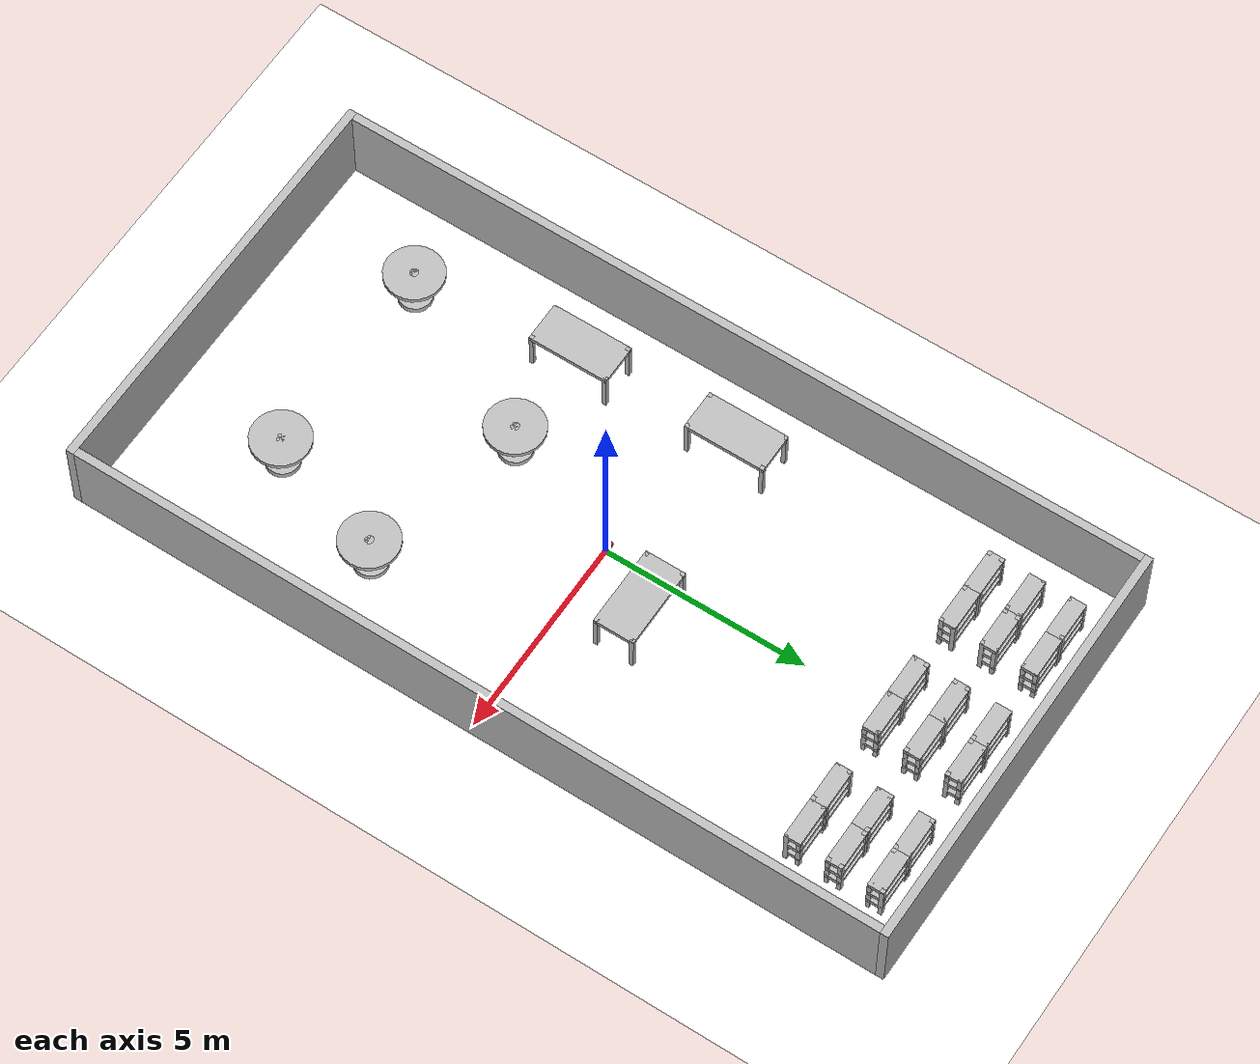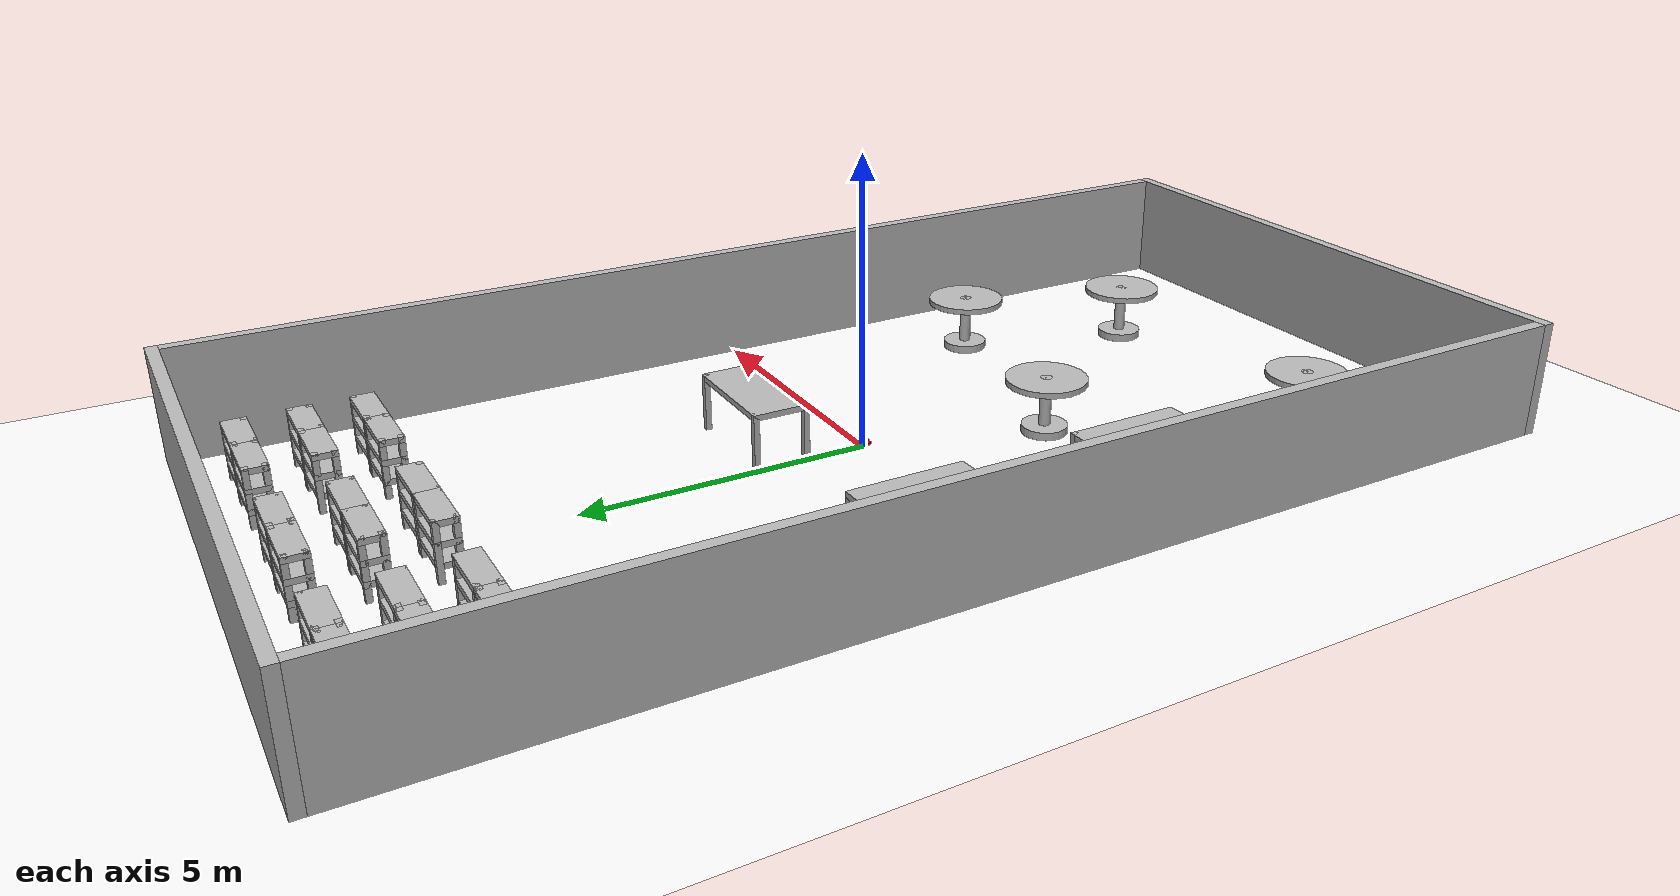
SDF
<?xml version='1.0'?>
<sdf version='1.11'>
  <world name='default'>

  <!-- NOTE including other world system plugins will disable the default ones -->

  <!-- DEFAULTS -->
  <plugin filename="gz-sim-user-commands-system" name="gz::sim::systems::UserCommands"></plugin>
  <plugin filename="gz-sim-physics-system" name="gz::sim::systems::Physics"></plugin>
  <plugin filename="gz-sim-sensors-system" name="gz::sim::systems::Sensors"></plugin>
  <plugin filename="gz-sim-scene-broadcaster-system" name="gz::sim::systems::SceneBroadcaster"></plugin>

	<plugin filename="gz-sim-imu-system" name="gz::sim::systems::Imu">
		<initial_orientation_as_reference>false</initial_orientation_as_reference>
	</plugin>

	<!-- TODO Add new RFID plugin here -->

	<include>
		<uri>file://robot.sdf</uri>
		<pose degrees='true'>0 0 0.1 0 0 0</pose>
	</include>

	<include>
		<uri>file://storelayout.sdf</uri>
	</include>

    <physics name="1ms" type="ignored">
      <max_step_size>0.001</max_step_size>
      <real_time_factor>1.0</real_time_factor>
    </physics>

    <light type="directional" name="sun">
      <cast_shadows>true</cast_shadows>
      <pose>0 0 10 0 0 0</pose>
      <diffuse>0.8 0.8 0.8 1</diffuse>
      <specular>0.2 0.2 0.2 1</specular>
      <attenuation>
        <range>1000</range>
        <constant>0.9</constant>
        <linear>0.01</linear>
        <quadratic>0.001</quadratic>
      </attenuation>
      <direction>-0.5 0.1 -0.9</direction>
    </light>

    <model name="ground_plane">
      <static>true</static>
      <link name="link">
        <collision name="collision">
          <geometry>
            <plane>
              <normal>0 0 1</normal>
              <size>100 100</size>
            </plane>
          </geometry>
        </collision>
        <visual name="visual">
          <geometry>
            <plane>
              <normal>0 0 1</normal>
              <size>100 100</size>
            </plane>
          </geometry>
          <material>
            <diffuse>1 1 1 1</diffuse>
          </material>
        </visual>
      </link>
    </model>

  </world>
</sdf>

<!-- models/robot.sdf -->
<sdf version='1.11'>
  <model name='robotmodel'>
    <link name='robot-base'>
      <pose>0 0 0 0 0 0</pose>
      <visual name='robot-base-v'>
        <!-- mesh -->
        <geometry>
          <mesh>
            <uri>file://robot_base.stl</uri>
            <scale>0.001 0.001 0.001</scale>
          </mesh>
        </geometry>
        <material>
          <diffuse>1 0 0 1</diffuse>
          <ambient>1 0 0 1</ambient>
          <!-- specular -->
        </material>
      </visual>
      <collision name='robot-base-c'>
        <geometry>
          <mesh>
            <uri>file://robot_base.stl</uri>
            <scale>0.001 0.001 0.001</scale>
          </mesh>
        </geometry>
      </collision>
      <inertial auto='true'>
        <mass>1000</mass>
      </inertial>
    </link>

		<link name='wheel-frontleft'>
      <pose degrees='true'>0.1 0.075 0 90 0 0</pose>
      <visual name='robot-frontleft-v'>
        <!-- mesh -->
        <geometry>
					<cylinder>
						<radius>0.02</radius>
						<length>0.02</length>
					</cylinder>
        </geometry>
        <material>
          <diffuse>1 0 0 1</diffuse>
          <ambient>1 0 0 1</ambient>
          <!-- specular -->
        </material>
      </visual>
      <collision name='robot-frontleft-c'>
        <geometry>
					<!-- NOTE Different geometries for collision and visual -->
					<sphere>
						<radius>0.02</radius>
					</sphere>
        </geometry>
      </collision>
      <inertial auto='true'>
        <mass>1</mass>
      </inertial>
	</link>

	<link name='wheel-backleft'>
      <pose degrees='true'>-0.1 0.075 0 -90 0 0</pose>
      <visual name='robot-backleft-v'>
        <!-- mesh -->
        <geometry>
					<cylinder>
						<radius>0.02</radius>
						<length>0.02</length>
					</cylinder>
        </geometry>
        <material>
          <diffuse>1 0 0 1</diffuse>
          <ambient>1 0 0 1</ambient>
          <!-- specular -->
        </material>
      </visual>
      <collision name='robot-backleft-c'>
        <geometry>
					<cylinder>
						<radius>0.02</radius>
						<length>0.02</length>
					</cylinder>
        </geometry>
      </collision>
      <inertial auto='true'>
        <mass>1</mass>
      </inertial>
	</link>

	<link name='wheel-frontright'>
      <pose degrees='true'>0.1 -0.075 0 90 0 0</pose>
      <visual name='robot-frontright-v'>
        <!-- mesh -->
        <geometry>
			<cylinder>
				<radius>0.02</radius>
				<length>0.02</length>
			</cylinder>
        </geometry>
        <material>
          <diffuse>1 0 0 1</diffuse>
          <ambient>1 0 0 1</ambient>
          <!-- specular -->
        </material>
      </visual>
      <collision name='robot-frontright-c'>
        <geometry>
					<!-- NOTE Different geometries for collision and visual -->
					<sphere>
						<radius>0.02</radius>
					</sphere>
        </geometry>
      </collision>
      <inertial auto='true'>
        <mass>1</mass>
      </inertial>
	</link>

	<link name='wheel-backright'>
      <pose degrees='true'>-0.1 -0.075 0 -90 0 0</pose>
      <visual name='robot-backright-v'>
        <!-- mesh -->
        <geometry>
			<cylinder>
				<radius>0.02</radius>
				<length>0.02</length>
			</cylinder>
        </geometry>
        <material>
          <diffuse>1 0 0 1</diffuse>
          <ambient>1 0 0 1</ambient>
          <!-- specular -->
        </material>
      </visual>
      <collision name='robot-backright-c'>
        <geometry>
			<cylinder>
				<radius>0.02</radius>
				<length>0.02</length>
			</cylinder>
        </geometry>
      </collision>
      <inertial auto='true'>
        <mass>1</mass>
      </inertial>
	</link>

    <joint name='frontleft' type='ball'>
      <pose>0 0 0 0 0 0</pose>
      <parent>robot-base</parent>
      <child>wheel-frontleft</child>
      <axis>
        <xyz>0 0 1</xyz>
      </axis>
    </joint>

    <joint name='frontright' type='ball'>
      <pose>0 0 0 0 0 0</pose>
      <parent>robot-base</parent>
      <child>wheel-frontright</child>
      <axis>
        <xyz>0 0 1</xyz>
      </axis>
    </joint>

    <joint name='backleft' type='revolute'>
      <pose>0 0 0 0 0 0</pose>
      <parent>robot-base</parent>
      <child>wheel-backleft</child>
      <axis>
        <xyz>0 0 1</xyz>
      </axis>
    </joint>

    <joint name='backright' type='revolute'>
      <pose>0 0 0 0 0 0</pose>
      <parent>robot-base</parent>
      <child>wheel-backright</child>
      <axis>
        <xyz>0 0 1</xyz>
      </axis>
    </joint>

	<link name='robot-lidar'>
		<pose>0 0 0.05 0 0 0</pose>
      <visual name='robot-lidar-v'>
        <!-- mesh -->
        <geometry>
			<cylinder>
				<radius>0.05 </radius>
				<length>0.02 </length>
			</cylinder>
        </geometry>
        <material>
          <diffuse>1 0 0 1</diffuse>
          <ambient>1 0 0 1</ambient>
          <!-- specular -->
        </material>
      </visual>
      <collision name='robot-base-c'>
        <geometry>
			<cylinder>
				<radius>0.05 </radius>
				<length>0.02 </length>
			</cylinder>
        </geometry>
      </collision>

		<sensor name='robot-lidar' type='gpu_lidar'>
			<topic>lidar</topic>
			<update_rate>5</update_rate>
			<always_on>true</always_on>
			<visualize>true</visualize>
			<ray>
				<scan>
					<horizontal>
						<samples>360</samples>
						<resolution>1.00</resolution>
						<min_angle>0.000</min_angle>
						<max_angle>6.280</max_angle>
					</horizontal>
				</scan>
				<range>
					<min>0.12</min>
					<max>10</max>
					<resolution>0.01500</resolution>
				</range>
        <noise>
          <type>gaussian</type>
          <mean>0.0</mean>
          <stddev>0.01</stddev>
        </noise>
			</ray>
		</sensor>
	</link>

    <joint name='lidarjoint' type='fixed'>
      <pose>0 0 0 0 0 0</pose>
      <parent>robot-base</parent>
      <child>robot-lidar</child>
      <axis>
        <xyz>1 0 0</xyz>
      </axis>
    </joint>

    <plugin filename="gz-sim-diff-drive-system" name="gz::sim::systems::DiffDrive">
        <left_joint>backleft</left_joint>
        <right_joint>backright</right_joint>
        <wheel_separation>0.15</wheel_separation>
        <wheel_radius>0.02</wheel_radius>

		<!-- Only change these to the frames if we want to use the wheel odom as a sole source -->
		<frame_id>odom</frame_id>
		<child_frame_id>base_link</child_frame_id>
		<tf_topic>/tf</tf_topic>

        <max_linear_acceleration>1</max_linear_acceleration>
        <min_linear_acceleration>-1</min_linear_acceleration>
        <max_angular_acceleration>2</max_angular_acceleration>
        <min_angular_acceleration>-2</min_angular_acceleration>
        <max_linear_velocity>0.5</max_linear_velocity>
        <min_linear_velocity>-0.5</min_linear_velocity>
        <max_angular_velocity>1</max_angular_velocity>
        <min_angular_velocity>-1</min_angular_velocity>
      </plugin>

	<link name="imu">
		<pose>0 0 0.1 0 0 0 </pose>
		<visual name="imu-v">
			<geometry>
				<box><size>0.02 0.02 0.02</size></box>
			</geometry>
		</visual>
		<collision name="imu-c">
			<geometry>
				<box><size>0.02 0.02 0.02</size></box>
			</geometry>
		</collision>

		<sensor name="imu-sensor" type="imu">
			<topic>imu</topic>
			<update_rate>100</update_rate>
			<always_on>true</always_on>
			<visualize>true</visualize>
			<imu>
        <angular_velocity>
          <x>
            <noise type="gaussian">
              <mean>0.0</mean>
              <stddev>2e-4</stddev>
              <bias_mean>0.0000075</bias_mean>
              <bias_stddev>0.0000008</bias_stddev>
            </noise>
          </x>
          <y>
            <noise type="gaussian">
              <mean>0.0</mean>
              <stddev>2e-4</stddev>
              <bias_mean>0.0000075</bias_mean>
              <bias_stddev>0.0000008</bias_stddev>
            </noise>
          </y>
          <z>
            <noise type="gaussian">
              <mean>0.0</mean>
              <stddev>2e-4</stddev>
              <bias_mean>0.0000075</bias_mean>
              <bias_stddev>0.0000008</bias_stddev>
            </noise>
          </z>
        </angular_velocity>
        <linear_acceleration>
          <x>
            <noise type="gaussian">
              <mean>0.0</mean>
              <stddev>1.7e-2</stddev>
              <bias_mean>0.1</bias_mean>
              <bias_stddev>0.001</bias_stddev>
            </noise>
          </x>
          <y>
            <noise type="gaussian">
              <mean>0.0</mean>
              <stddev>1.7e-2</stddev>
              <bias_mean>0.1</bias_mean>
              <bias_stddev>0.001</bias_stddev>
            </noise>
          </y>
          <z>
            <noise type="gaussian">
              <mean>0.0</mean>
              <stddev>1.7e-2</stddev>
              <bias_mean>0.1</bias_mean>
              <bias_stddev>0.001</bias_stddev>
            </noise>
          </z>
        </linear_acceleration>
      </imu>
		</sensor>
	</link>

    <joint name='imujoint' type='fixed'>
      <pose>0 0 0 0 0 0</pose>
      <parent>robot-base</parent>
      <child>imu</child>
      <axis>
        <xyz>1 0 0</xyz>
      </axis>
    </joint>

  </model>
</sdf>

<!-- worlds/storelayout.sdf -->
<sdf version="1.11">
 <model name="store-model">
  <static>true</static>
  <link name="store-shelf-l0-shelf0">
   <pose>2.5 9.2 0.95 0 0 0</pose>
   <visual name="store-shelf-v0-shelf0">
    <geometry>
     <box>
      <size>1 0.4 0.1</size>
     </box>
    </geometry>
    <material>
     <diffuse>0.726 0.726 0.726 1</diffuse>
     <ambient>0.726 0.726 0.726 1</ambient>
     <specular>0.726 0.726 0.726 1</specular>
    </material>
   </visual>
   <collision name="store-shelf-c0-shelf0">
    <geometry>
     <box>
      <size>1 0.4 0.1</size>
     </box>
    </geometry>
   </collision>
  </link>
  <link name="store-shelf-l0-shelf1">
   <pose>2.5 9.2 0.6166666666666666 0 0 0</pose>
   <visual name="store-shelf-v0-shelf1">
    <geometry>
     <box>
      <size>1 0.4 0.1</size>
     </box>
    </geometry>
    <material>
     <diffuse>0.726 0.726 0.726 1</diffuse>
     <ambient>0.726 0.726 0.726 1</ambient>
     <specular>0.726 0.726 0.726 1</specular>
    </material>
   </visual>
   <collision name="store-shelf-c0-shelf1">
    <geometry>
     <box>
      <size>1 0.4 0.1</size>
     </box>
    </geometry>
   </collision>
  </link>
  <link name="store-shelf-l0-shelf2">
   <pose>2.5 9.2 0.2833333333333333 0 0 0</pose>
   <visual name="store-shelf-v0-shelf2">
    <geometry>
     <box>
      <size>1 0.4 0.1</size>
     </box>
    </geometry>
    <material>
     <diffuse>0.726 0.726 0.726 1</diffuse>
     <ambient>0.726 0.726 0.726 1</ambient>
     <specular>0.726 0.726 0.726 1</specular>
    </material>
   </visual>
   <collision name="store-shelf-c0-shelf2">
    <geometry>
     <box>
      <size>1 0.4 0.1</size>
     </box>
    </geometry>
   </collision>
  </link>
  <link name="store-shelf-l0-support0">
   <pose>2.05 9.05 0.5 0 0 0</pose>
   <visual name="store-shelf-v0-support0">
    <geometry>
     <box>
      <size>0.1 0.1 1</size>
     </box>
    </geometry>
    <material>
     <diffuse>0.726 0.726 0.726 1</diffuse>
     <ambient>0.726 0.726 0.726 1</ambient>
     <specular>0.726 0.726 0.726 1</specular>
    </material>
   </visual>
   <collision name="store-shelf-c0-support0">
    <geometry>
     <box>
      <size>0.1 0.1 1</size>
     </box>
    </geometry>
   </collision>
  </link>
  <link name="store-shelf-l0-support1">
   <pose>2.95 9.05 0.5 0 0 0</pose>
   <visual name="store-shelf-v0-support1">
    <geometry>
     <box>
      <size>0.1 0.1 1</size>
     </box>
    </geometry>
    <material>
     <diffuse>0.726 0.726 0.726 1</diffuse>
     <ambient>0.726 0.726 0.726 1</ambient>
     <specular>0.726 0.726 0.726 1</specular>
    </material>
   </visual>
   <collision name="store-shelf-c0-support1">
    <geometry>
     <box>
      <size>0.1 0.1 1</size>
     </box>
    </geometry>
   </collision>
  </link>
  <link name="store-shelf-l0-support2">
   <pose>2.05 9.35 0.5 0 0 0</pose>
   <visual name="store-shelf-v0-support2">
    <geometry>
     <box>
      <size>0.1 0.1 1</size>
     </box>
    </geometry>
    <material>
     <diffuse>0.726 0.726 0.726 1</diffuse>
     <ambient>0.726 0.726 0.726 1</ambient>
     <specular>0.726 0.726 0.726 1</specular>
    </material>
   </visual>
   <collision name="store-shelf-c0-support2">
    <geometry>
     <box>
      <size>0.1 0.1 1</size>
     </box>
    </geometry>
   </collision>
  </link>
  <link name="store-shelf-l0-support3">
   <pose>2.95 9.35 0.5 0 0 0</pose>
   <visual name="store-shelf-v0-support3">
    <geometry>
     <box>
      <size>0.1 0.1 1</size>
     </box>
    </geometry>
    <material>
     <diffuse>0.726 0.726 0.726 1</diffuse>
     <ambient>0.726 0.726 0.726 1</ambient>
     <specular>0.726 0.726 0.726 1</specular>
    </material>
   </visual>
   <collision name="store-shelf-c0-support3">
    <geometry>
     <box>
      <size>0.1 0.1 1</size>
     </box>
    </geometry>
   </collision>
  </link>
  <link name="store-shelf-l1-shelf0">
   <pose>2.5 8.2 0.95 0 0 0</pose>
   <visual name="store-shelf-v1-shelf0">
    <geometry>
     <box>
      <size>1 0.4 0.1</size>
     </box>
    </geometry>
    <material>
     <diffuse>0.726 0.726 0.726 1</diffuse>
     <ambient>0.726 0.726 0.726 1</ambient>
     <specular>0.726 0.726 0.726 1</specular>
    </material>
   </visual>
   <collision name="store-shelf-c1-shelf0">
    <geometry>
     <box>
      <size>1 0.4 0.1</size>
     </box>
    </geometry>
   </collision>
  </link>
  <link name="store-shelf-l1-shelf1">
   <pose>2.5 8.2 0.6166666666666666 0 0 0</pose>
   <visual name="store-shelf-v1-shelf1">
    <geometry>
     <box>
      <size>1 0.4 0.1</size>
     </box>
    </geometry>
    <material>
     <diffuse>0.726 0.726 0.726 1</diffuse>
     <ambient>0.726 0.726 0.726 1</ambient>
     <specular>0.726 0.726 0.726 1</specular>
    </material>
   </visual>
   <collision name="store-shelf-c1-shelf1">
    <geometry>
     <box>
      <size>1 0.4 0.1</size>
     </box>
    </geometry>
   </collision>
  </link>
  <link name="store-shelf-l1-shelf2">
   <pose>2.5 8.2 0.2833333333333333 0 0 0</pose>
   <visual name="store-shelf-v1-shelf2">
    <geometry>
     <box>
      <size>1 0.4 0.1</size>
     </box>
    </geometry>
    <material>
     <diffuse>0.726 0.726 0.726 1</diffuse>
     <ambient>0.726 0.726 0.726 1</ambient>
     <specular>0.726 0.726 0.726 1</specular>
    </material>
   </visual>
   <collision name="store-shelf-c1-shelf2">
    <geometry>
     <box>
      <size>1 0.4 0.1</size>
     </box>
    </geometry>
   </collision>
  </link>
  <link name="store-shelf-l1-support0">
   <pose>2.05 8.05 0.5 0 0 0</pose>
   <visual name="store-shelf-v1-support0">
    <geometry>
     <box>
      <size>0.1 0.1 1</size>
     </box>
    </geometry>
    <material>
     <diffuse>0.726 0.726 0.726 1</diffuse>
     <ambient>0.726 0.726 0.726 1</ambient>
     <specular>0.726 0.726 0.726 1</specular>
    </material>
   </visual>
   <collision name="store-shelf-c1-support0">
    <geometry>
     <box>
      <size>0.1 0.1 1</size>
     </box>
    </geometry>
   </collision>
  </link>
  <link name="store-shelf-l1-support1">
   <pose>2.95 8.05 0.5 0 0 0</pose>
   <visual name="store-shelf-v1-support1">
    <geometry>
     <box>
      <size>0.1 0.1 1</size>
     </box>
    </geometry>
    <material>
     <diffuse>0.726 0.726 0.726 1</diffuse>
     <ambient>0.726 0.726 0.726 1</ambient>
     <specular>0.726 0.726 0.726 1</specular>
    </material>
   </visual>
   <collision name="store-shelf-c1-support1">
    <geometry>
     <box>
      <size>0.1 0.1 1</size>
     </box>
    </geometry>
   </collision>
  </link>
  <link name="store-shelf-l1-support2">
   <pose>2.05 8.35 0.5 0 0 0</pose>
   <visual name="store-shelf-v1-support2">
    <geometry>
     <box>
      <size>0.1 0.1 1</size>
     </box>
    </geometry>
    <material>
     <diffuse>0.726 0.726 0.726 1</diffuse>
     <ambient>0.726 0.726 0.726 1</ambient>
     <specular>0.726 0.726 0.726 1</specular>
    </material>
   </visual>
   <collision name="store-shelf-c1-support2">
    <geometry>
     <box>
      <size>0.1 0.1 1</size>
     </box>
    </geometry>
   </collision>
  </link>
  <link name="store-shelf-l1-support3">
   <pose>2.95 8.35 0.5 0 0 0</pose>
   <visual name="store-shelf-v1-support3">
    <geometry>
     <box>
      <size>0.1 0.1 1</size>
     </box>
    </geometry>
    <material>
     <diffuse>0.726 0.726 0.726 1</diffuse>
     <ambient>0.726 0.726 0.726 1</ambient>
     <specular>0.726 0.726 0.726 1</specular>
    </material>
   </visual>
   <collision name="store-shelf-c1-support3">
    <geometry>
     <box>
      <size>0.1 0.1 1</size>
     </box>
    </geometry>
   </collision>
  </link>
  <link name="store-shelf-l2-shelf0">
   <pose>2.5 7.2 0.95 0 0 0</pose>
   <visual name="store-shelf-v2-shelf0">
    <geometry>
     <box>
      <size>1 0.4 0.1</size>
     </box>
    </geometry>
    <material>
     <diffuse>0.726 0.726 0.726 1</diffuse>
     <ambient>0.726 0.726 0.726 1</ambient>
     <specular>0.726 0.726 0.726 1</specular>
    </material>
   </visual>
   <collision name="store-shelf-c2-shelf0">
    <geometry>
     <box>
      <size>1 0.4 0.1</size>
     </box>
    </geometry>
   </collision>
  </link>
  <link name="store-shelf-l2-shelf1">
   <pose>2.5 7.2 0.6166666666666666 0 0 0</pose>
   <visual name="store-shelf-v2-shelf1">
    <geometry>
     <box>
      <size>1 0.4 0.1</size>
     </box>
    </geometry>
    <material>
     <diffuse>0.726 0.726 0.726 1</diffuse>
     <ambient>0.726 0.726 0.726 1</ambient>
     <specular>0.726 0.726 0.726 1</specular>
    </material>
   </visual>
   <collision name="store-shelf-c2-shelf1">
    <geometry>
     <box>
      <size>1 0.4 0.1</size>
     </box>
    </geometry>
   </collision>
  </link>
  <link name="store-shelf-l2-shelf2">
   <pose>2.5 7.2 0.2833333333333333 0 0 0</pose>
   <visual name="store-shelf-v2-shelf2">
    <geometry>
     <box>
      <size>1 0.4 0.1</size>
     </box>
    </geometry>
    <material>
     <diffuse>0.726 0.726 0.726 1</diffuse>
     <ambient>0.726 0.726 0.726 1</ambient>
     <specular>0.726 0.726 0.726 1</specular>
    </material>
   </visual>
   <collision name="store-shelf-c2-shelf2">
    <geometry>
     <box>
      <size>1 0.4 0.1</size>
     </box>
    </geometry>
   </collision>
  </link>
  <link name="store-shelf-l2-support0">
   <pose>2.05 7.05 0.5 0 0 0</pose>
   <visual name="store-shelf-v2-support0">
    <geometry>
     <box>
      <size>0.1 0.1 1</size>
     </box>
    </geometry>
    <material>
     <diffuse>0.726 0.726 0.726 1</diffuse>
     <ambient>0.726 0.726 0.726 1</ambient>
     <specular>0.726 0.726 0.726 1</specular>
    </material>
   </visual>
   <collision name="store-shelf-c2-support0">
    <geometry>
     <box>
      <size>0.1 0.1 1</size>
     </box>
    </geometry>
   </collision>
  </link>
  <link name="store-shelf-l2-support1">
   <pose>2.95 7.05 0.5 0 0 0</pose>
   <visual name="store-shelf-v2-support1">
    <geometry>
     <box>
      <size>0.1 0.1 1</size>
     </box>
    </geometry>
    <material>
     <diffuse>0.726 0.726 0.726 1</diffuse>
     <ambient>0.726 0.726 0.726 1</ambient>
     <specular>0.726 0.726 0.726 1</specular>
    </material>
   </visual>
   <collision name="store-shelf-c2-support1">
    <geometry>
     <box>
      <size>0.1 0.1 1</size>
     </box>
    </geometry>
   </collision>
  </link>
  <link name="store-shelf-l2-support2">
   <pose>2.05 7.3500000000000005 0.5 0 0 0</pose>
   <visual name="store-shelf-v2-support2">
    <geometry>
     <box>
      <size>0.1 0.1 1</size>
     </box>
    </geometry>
    <material>
     <diffuse>0.726 0.726 0.726 1</diffuse>
     <ambient>0.726 0.726 0.726 1</ambient>
     <specular>0.726 0.726 0.726 1</specular>
    </material>
   </visual>
   <collision name="store-shelf-c2-support2">
    <geometry>
     <box>
      <size>0.1 0.1 1</size>
     </box>
    </geometry>
   </collision>
  </link>
  <link name="store-shelf-l2-support3">
   <pose>2.95 7.3500000000000005 0.5 0 0 0</pose>
   <visual name="store-shelf-v2-support3">
    <geometry>
     <box>
      <size>0.1 0.1 1</size>
     </box>
    </geometry>
    <material>
     <diffuse>0.726 0.726 0.726 1</diffuse>
     <ambient>0.726 0.726 0.726 1</ambient>
     <specular>0.726 0.726 0.726 1</specular>
    </material>
   </visual>
   <collision name="store-shelf-c2-support3">
    <geometry>
     <box>
      <size>0.1 0.1 1</size>
     </box>
    </geometry>
   </collision>
  </link>
  <link name="store-shelf-l3-shelf0">
   <pose>3.5 7.2 0.95 0 0 0</pose>
   <visual name="store-shelf-v3-shelf0">
    <geometry>
     <box>
      <size>1 0.4 0.1</size>
     </box>
    </geometry>
    <material>
     <diffuse>0.726 0.726 0.726 1</diffuse>
     <ambient>0.726 0.726 0.726 1</ambient>
     <specular>0.726 0.726 0.726 1</specular>
    </material>
   </visual>
   <collision name="store-shelf-c3-shelf0">
    <geometry>
     <box>
      <size>1 0.4 0.1</size>
     </box>
    </geometry>
   </collision>
  </link>
  <link name="store-shelf-l3-shelf1">
   <pose>3.5 7.2 0.6166666666666666 0 0 0</pose>
   <visual name="store-shelf-v3-shelf1">
    <geometry>
     <box>
      <size>1 0.4 0.1</size>
     </box>
    </geometry>
    <material>
     <diffuse>0.726 0.726 0.726 1</diffuse>
     <ambient>0.726 0.726 0.726 1</ambient>
     <specular>0.726 0.726 0.726 1</specular>
    </material>
   </visual>
   <collision name="store-shelf-c3-shelf1">
    <geometry>
     <box>
      <size>1 0.4 0.1</size>
     </box>
    </geometry>
   </collision>
  </link>
  <link name="store-shelf-l3-shelf2">
   <pose>3.5 7.2 0.2833333333333333 0 0 0</pose>
   <visual name="store-shelf-v3-shelf2">
    <geometry>
     <box>
      <size>1 0.4 0.1</size>
     </box>
    </geometry>
    <material>
     <diffuse>0.726 0.726 0.726 1</diffuse>
     <ambient>0.726 0.726 0.726 1</ambient>
     <specular>0.726 0.726 0.726 1</specular>
    </material>
   </visual>
   <collision name="store-shelf-c3-shelf2">
    <geometry>
     <box>
      <size>1 0.4 0.1</size>
     </box>
    </geometry>
   </collision>
  </link>
  <link name="store-shelf-l3-support0">
   <pose>3.05 7.05 0.5 0 0 0</pose>
   <visual name="store-shelf-v3-support0">
    <geometry>
     <box>
      <size>0.1 0.1 1</size>
     </box>
    </geometry>
    <material>
     <diffuse>0.726 0.726 0.726 1</diffuse>
     <ambient>0.726 0.726 0.726 1</ambient>
     <specular>0.726 0.726 0.726 1</specular>
    </material>
   </visual>
   <collision name="store-shelf-c3-support0">
    <geometry>
     <box>
      <size>0.1 0.1 1</size>
     </box>
    </geometry>
   </collision>
  </link>
  <link name="store-shelf-l3-support1">
   <pose>3.95 7.05 0.5 0 0 0</pose>
   <visual name="store-shelf-v3-support1">
    <geometry>
     <box>
      <size>0.1 0.1 1</size>
     </box>
    </geometry>
    <material>
     <diffuse>0.726 0.726 0.726 1</diffuse>
     <ambient>0.726 0.726 0.726 1</ambient>
     <specular>0.726 0.726 0.726 1</specular>
    </material>
   </visual>
   <collision name="store-shelf-c3-support1">
    <geometry>
     <box>
      <size>0.1 0.1 1</size>
     </box>
    </geometry>
   </collision>
  </link>
  <link name="store-shelf-l3-support2">
   <pose>3.05 7.3500000000000005 0.5 0 0 0</pose>
   <visual name="store-shelf-v3-support2">
    <geometry>
     <box>
      <size>0.1 0.1 1</size>
     </box>
    </geometry>
    <material>
     <diffuse>0.726 0.726 0.726 1</diffuse>
     <ambient>0.726 0.726 0.726 1</ambient>
     <specular>0.726 0.726 0.726 1</specular>
    </material>
   </visual>
   <collision name="store-shelf-c3-support2">
    <geometry>
     <box>
      <size>0.1 0.1 1</size>
     </box>
    </geometry>
   </collision>
  </link>
  <link name="store-shelf-l3-support3">
   <pose>3.95 7.3500000000000005 0.5 0 0 0</pose>
   <visual name="store-shelf-v3-support3">
    <geometry>
     <box>
      <size>0.1 0.1 1</size>
     </box>
    </geometry>
    <material>
     <diffuse>0.726 0.726 0.726 1</diffuse>
     <ambient>0.726 0.726 0.726 1</ambient>
     <specular>0.726 0.726 0.726 1</specular>
    </material>
   </visual>
   <collision name="store-shelf-c3-support3">
    <geometry>
     <box>
      <size>0.1 0.1 1</size>
     </box>
    </geometry>
   </collision>
  </link>
  <link name="store-shelf-l4-shelf0">
   <pose>3.5 8.2 0.95 0 0 0</pose>
   <visual name="store-shelf-v4-shelf0">
    <geometry>
     <box>
      <size>1 0.4 0.1</size>
     </box>
    </geometry>
    <material>
     <diffuse>0.726 0.726 0.726 1</diffuse>
     <ambient>0.726 0.726 0.726 1</ambient>
     <specular>0.726 0.726 0.726 1</specular>
    </material>
   </visual>
   <collision name="store-shelf-c4-shelf0">
    <geometry>
     <box>
      <size>1 0.4 0.1</size>
     </box>
    </geometry>
   </collision>
  </link>
  <link name="store-shelf-l4-shelf1">
   <pose>3.5 8.2 0.6166666666666666 0 0 0</pose>
   <visual name="store-shelf-v4-shelf1">
    <geometry>
     <box>
      <size>1 0.4 0.1</size>
     </box>
    </geometry>
    <material>
     <diffuse>0.726 0.726 0.726 1</diffuse>
     <ambient>0.726 0.726 0.726 1</ambient>
     <specular>0.726 0.726 0.726 1</specular>
    </material>
   </visual>
   <collision name="store-shelf-c4-shelf1">
    <geometry>
     <box>
      <size>1 0.4 0.1</size>
     </box>
    </geometry>
   </collision>
  </link>
  <link name="store-shelf-l4-shelf2">
   <pose>3.5 8.2 0.2833333333333333 0 0 0</pose>
   <visual name="store-shelf-v4-shelf2">
    <geometry>
     <box>
      <size>1 0.4 0.1</size>
     </box>
    </geometry>
    <material>
     <diffuse>0.726 0.726 0.726 1</diffuse>
     <ambient>0.726 0.726 0.726 1</ambient>
     <specular>0.726 0.726 0.726 1</specular>
    </material>
   </visual>
   <collision name="store-shelf-c4-shelf2">
    <geometry>
     <box>
      <size>1 0.4 0.1</size>
     </box>
    </geometry>
   </collision>
  </link>
  <link name="store-shelf-l4-support0">
   <pose>3.05 8.05 0.5 0 0 0</pose>
   <visual name="store-shelf-v4-support0">
    <geometry>
     <box>
      <size>0.1 0.1 1</size>
     </box>
    </geometry>
    <material>
     <diffuse>0.726 0.726 0.726 1</diffuse>
     <ambient>0.726 0.726 0.726 1</ambient>
     <specular>0.726 0.726 0.726 1</specular>
    </material>
   </visual>
   <collision name="store-shelf-c4-support0">
    <geometry>
     <box>
      <size>0.1 0.1 1</size>
     </box>
    </geometry>
   </collision>
  </link>
  <link name="store-shelf-l4-support1">
   <pose>3.95 8.05 0.5 0 0 0</pose>
   <visual name="store-shelf-v4-support1">
    <geometry>
     <box>
      <size>0.1 0.1 1</size>
     </box>
    </geometry>
    <material>
     <diffuse>0.726 0.726 0.726 1</diffuse>
     <ambient>0.726 0.726 0.726 1</ambient>
     <specular>0.726 0.726 0.726 1</specular>
    </material>
   </visual>
   <collision name="store-shelf-c4-support1">
    <geometry>
     <box>
      <size>0.1 0.1 1</size>
     </box>
    </geometry>
   </collision>
  </link>
  <link name="store-shelf-l4-support2">
   <pose>3.05 8.35 0.5 0 0 0</pose>
   <visual name="store-shelf-v4-support2">
    <geometry>
     <box>
      <size>0.1 0.1 1</size>
     </box>
    </geometry>
    <material>
     <diffuse>0.726 0.726 0.726 1</diffuse>
     <ambient>0.726 0.726 0.726 1</ambient>
     <specular>0.726 0.726 0.726 1</specular>
    </material>
   </visual>
   <collision name="store-shelf-c4-support2">
    <geometry>
     <box>
      <size>0.1 0.1 1</size>
     </box>
    </geometry>
   </collision>
  </link>
  <link name="store-shelf-l4-support3">
   <pose>3.95 8.35 0.5 0 0 0</pose>
   <visual name="store-shelf-v4-support3">
    <geometry>
     <box>
      <size>0.1 0.1 1</size>
     </box>
    </geometry>
    <material>
     <diffuse>0.726 0.726 0.726 1</diffuse>
     <ambient>0.726 0.726 0.726 1</ambient>
     <specular>0.726 0.726 0.726 1</specular>
    </material>
   </visual>
   <collision name="store-shelf-c4-support3">
    <geometry>
     <box>
      <size>0.1 0.1 1</size>
     </box>
    </geometry>
   </collision>
  </link>
  <link name="store-shelf-l5-shelf0">
   <pose>3.5 9.2 0.95 0 0 0</pose>
   <visual name="store-shelf-v5-shelf0">
    <geometry>
     <box>
      <size>1 0.4 0.1</size>
     </box>
    </geometry>
    <material>
     <diffuse>0.726 0.726 0.726 1</diffuse>
     <ambient>0.726 0.726 0.726 1</ambient>
     <specular>0.726 0.726 0.726 1</specular>
    </material>
   </visual>
   <collision name="store-shelf-c5-shelf0">
    <geometry>
     <box>
      <size>1 0.4 0.1</size>
     </box>
    </geometry>
   </collision>
  </link>
  <link name="store-shelf-l5-shelf1">
   <pose>3.5 9.2 0.6166666666666666 0 0 0</pose>
   <visual name="store-shelf-v5-shelf1">
    <geometry>
     <box>
      <size>1 0.4 0.1</size>
     </box>
    </geometry>
    <material>
     <diffuse>0.726 0.726 0.726 1</diffuse>
     <ambient>0.726 0.726 0.726 1</ambient>
     <specular>0.726 0.726 0.726 1</specular>
    </material>
   </visual>
   <collision name="store-shelf-c5-shelf1">
    <geometry>
     <box>
      <size>1 0.4 0.1</size>
     </box>
    </geometry>
   </collision>
  </link>
  <link name="store-shelf-l5-shelf2">
   <pose>3.5 9.2 0.2833333333333333 0 0 0</pose>
   <visual name="store-shelf-v5-shelf2">
    <geometry>
     <box>
      <size>1 0.4 0.1</size>
     </box>
    </geometry>
    <material>
     <diffuse>0.726 0.726 0.726 1</diffuse>
     <ambient>0.726 0.726 0.726 1</ambient>
     <specular>0.726 0.726 0.726 1</specular>
    </material>
   </visual>
   <collision name="store-shelf-c5-shelf2">
    <geometry>
     <box>
      <size>1 0.4 0.1</size>
     </box>
    </geometry>
   </collision>
  </link>
  <link name="store-shelf-l5-support0">
   <pose>3.05 9.05 0.5 0 0 0</pose>
   <visual name="store-shelf-v5-support0">
    <geometry>
     <box>
      <size>0.1 0.1 1</size>
     </box>
    </geometry>
    <material>
     <diffuse>0.726 0.726 0.726 1</diffuse>
     <ambient>0.726 0.726 0.726 1</ambient>
     <specular>0.726 0.726 0.726 1</specular>
    </material>
   </visual>
   <collision name="store-shelf-c5-support0">
    <geometry>
     <box>
      <size>0.1 0.1 1</size>
     </box>
    </geometry>
   </collision>
  </link>
  <link name="store-shelf-l5-support1">
   <pose>3.95 9.05 0.5 0 0 0</pose>
   <visual name="store-shelf-v5-support1">
    <geometry>
     <box>
      <size>0.1 0.1 1</size>
     </box>
    </geometry>
    <material>
     <diffuse>0.726 0.726 0.726 1</diffuse>
     <ambient>0.726 0.726 0.726 1</ambient>
     <specular>0.726 0.726 0.726 1</specular>
    </material>
   </visual>
   <collision name="store-shelf-c5-support1">
    <geometry>
     <box>
      <size>0.1 0.1 1</size>
     </box>
    </geometry>
   </collision>
  </link>
  <link name="store-shelf-l5-support2">
   <pose>3.05 9.35 0.5 0 0 0</pose>
   <visual name="store-shelf-v5-support2">
    <geometry>
     <box>
      <size>0.1 0.1 1</size>
     </box>
    </geometry>
    <material>
     <diffuse>0.726 0.726 0.726 1</diffuse>
     <ambient>0.726 0.726 0.726 1</ambient>
     <specular>0.726 0.726 0.726 1</specular>
    </material>
   </visual>
   <collision name="store-shelf-c5-support2">
    <geometry>
     <box>
      <size>0.1 0.1 1</size>
     </box>
    </geometry>
   </collision>
  </link>
  <link name="store-shelf-l5-support3">
   <pose>3.95 9.35 0.5 0 0 0</pose>
   <visual name="store-shelf-v5-support3">
    <geometry>
     <box>
      <size>0.1 0.1 1</size>
     </box>
    </geometry>
    <material>
     <diffuse>0.726 0.726 0.726 1</diffuse>
     <ambient>0.726 0.726 0.726 1</ambient>
     <specular>0.726 0.726 0.726 1</specular>
    </material>
   </visual>
   <collision name="store-shelf-c5-support3">
    <geometry>
     <box>
      <size>0.1 0.1 1</size>
     </box>
    </geometry>
   </collision>
  </link>
  <link name="store-shelf-l6-shelf0">
   <pose>-0.5 7.2 0.95 0 0 0</pose>
   <visual name="store-shelf-v6-shelf0">
    <geometry>
     <box>
      <size>1 0.4 0.1</size>
     </box>
    </geometry>
    <material>
     <diffuse>0.726 0.726 0.726 1</diffuse>
     <ambient>0.726 0.726 0.726 1</ambient>
     <specular>0.726 0.726 0.726 1</specular>
    </material>
   </visual>
   <collision name="store-shelf-c6-shelf0">
    <geometry>
     <box>
      <size>1 0.4 0.1</size>
     </box>
    </geometry>
   </collision>
  </link>
  <link name="store-shelf-l6-shelf1">
   <pose>-0.5 7.2 0.6166666666666666 0 0 0</pose>
   <visual name="store-shelf-v6-shelf1">
    <geometry>
     <box>
      <size>1 0.4 0.1</size>
     </box>
    </geometry>
    <material>
     <diffuse>0.726 0.726 0.726 1</diffuse>
     <ambient>0.726 0.726 0.726 1</ambient>
     <specular>0.726 0.726 0.726 1</specular>
    </material>
   </visual>
   <collision name="store-shelf-c6-shelf1">
    <geometry>
     <box>
      <size>1 0.4 0.1</size>
     </box>
    </geometry>
   </collision>
  </link>
  <link name="store-shelf-l6-shelf2">
   <pose>-0.5 7.2 0.2833333333333333 0 0 0</pose>
   <visual name="store-shelf-v6-shelf2">
    <geometry>
     <box>
      <size>1 0.4 0.1</size>
     </box>
    </geometry>
    <material>
     <diffuse>0.726 0.726 0.726 1</diffuse>
     <ambient>0.726 0.726 0.726 1</ambient>
     <specular>0.726 0.726 0.726 1</specular>
    </material>
   </visual>
   <collision name="store-shelf-c6-shelf2">
    <geometry>
     <box>
      <size>1 0.4 0.1</size>
     </box>
    </geometry>
   </collision>
  </link>
  <link name="store-shelf-l6-support0">
   <pose>-0.95 7.05 0.5 0 0 0</pose>
   <visual name="store-shelf-v6-support0">
    <geometry>
     <box>
      <size>0.1 0.1 1</size>
     </box>
    </geometry>
    <material>
     <diffuse>0.726 0.726 0.726 1</diffuse>
     <ambient>0.726 0.726 0.726 1</ambient>
     <specular>0.726 0.726 0.726 1</specular>
    </material>
   </visual>
   <collision name="store-shelf-c6-support0">
    <geometry>
     <box>
      <size>0.1 0.1 1</size>
     </box>
    </geometry>
   </collision>
  </link>
  <link name="store-shelf-l6-support1">
   <pose>-0.05 7.05 0.5 0 0 0</pose>
   <visual name="store-shelf-v6-support1">
    <geometry>
     <box>
      <size>0.1 0.1 1</size>
     </box>
    </geometry>
    <material>
     <diffuse>0.726 0.726 0.726 1</diffuse>
     <ambient>0.726 0.726 0.726 1</ambient>
     <specular>0.726 0.726 0.726 1</specular>
    </material>
   </visual>
   <collision name="store-shelf-c6-support1">
    <geometry>
     <box>
      <size>0.1 0.1 1</size>
     </box>
    </geometry>
   </collision>
  </link>
  <link name="store-shelf-l6-support2">
   <pose>-0.95 7.3500000000000005 0.5 0 0 0</pose>
   <visual name="store-shelf-v6-support2">
    <geometry>
     <box>
      <size>0.1 0.1 1</size>
     </box>
    </geometry>
    <material>
     <diffuse>0.726 0.726 0.726 1</diffuse>
     <ambient>0.726 0.726 0.726 1</ambient>
     <specular>0.726 0.726 0.726 1</specular>
    </material>
   </visual>
   <collision name="store-shelf-c6-support2">
    <geometry>
     <box>
      <size>0.1 0.1 1</size>
     </box>
    </geometry>
   </collision>
  </link>
  <link name="store-shelf-l6-support3">
   <pose>-0.05 7.3500000000000005 0.5 0 0 0</pose>
   <visual name="store-shelf-v6-support3">
    <geometry>
     <box>
      <size>0.1 0.1 1</size>
     </box>
    </geometry>
    <material>
     <diffuse>0.726 0.726 0.726 1</diffuse>
     <ambient>0.726 0.726 0.726 1</ambient>
     <specular>0.726 0.726 0.726 1</specular>
    </material>
   </visual>
   <collision name="store-shelf-c6-support3">
    <geometry>
     <box>
      <size>0.1 0.1 1</size>
     </box>
    </geometry>
   </collision>
  </link>
  <link name="store-shelf-l7-shelf0">
   <pose>-0.5 8.2 0.95 0 0 0</pose>
   <visual name="store-shelf-v7-shelf0">
    <geometry>
     <box>
      <size>1 0.4 0.1</size>
     </box>
    </geometry>
    <material>
     <diffuse>0.726 0.726 0.726 1</diffuse>
     <ambient>0.726 0.726 0.726 1</ambient>
     <specular>0.726 0.726 0.726 1</specular>
    </material>
   </visual>
   <collision name="store-shelf-c7-shelf0">
    <geometry>
     <box>
      <size>1 0.4 0.1</size>
     </box>
    </geometry>
   </collision>
  </link>
  <link name="store-shelf-l7-shelf1">
   <pose>-0.5 8.2 0.6166666666666666 0 0 0</pose>
   <visual name="store-shelf-v7-shelf1">
    <geometry>
     <box>
      <size>1 0.4 0.1</size>
     </box>
    </geometry>
    <material>
     <diffuse>0.726 0.726 0.726 1</diffuse>
     <ambient>0.726 0.726 0.726 1</ambient>
     <specular>0.726 0.726 0.726 1</specular>
    </material>
   </visual>
   <collision name="store-shelf-c7-shelf1">
    <geometry>
     <box>
      <size>1 0.4 0.1</size>
     </box>
    </geometry>
   </collision>
  </link>
  <link name="store-shelf-l7-shelf2">
   <pose>-0.5 8.2 0.2833333333333333 0 0 0</pose>
   <visual name="store-shelf-v7-shelf2">
    <geometry>
     <box>
      <size>1 0.4 0.1</size>
     </box>
    </geometry>
    <material>
     <diffuse>0.726 0.726 0.726 1</diffuse>
     <ambient>0.726 0.726 0.726 1</ambient>
     <specular>0.726 0.726 0.726 1</specular>
    </material>
   </visual>
   <collision name="store-shelf-c7-shelf2">
    <geometry>
     <box>
      <size>1 0.4 0.1</size>
     </box>
    </geometry>
   </collision>
  </link>
  <link name="store-shelf-l7-support0">
   <pose>-0.95 8.05 0.5 0 0 0</pose>
   <visual name="store-shelf-v7-support0">
    <geometry>
     <box>
      <size>0.1 0.1 1</size>
     </box>
    </geometry>
    <material>
     <diffuse>0.726 0.726 0.726 1</diffuse>
     <ambient>0.726 0.726 0.726 1</ambient>
     <specular>0.726 0.726 0.726 1</specular>
    </material>
   </visual>
   <collision name="store-shelf-c7-support0">
    <geometry>
     <box>
      <size>0.1 0.1 1</size>
     </box>
    </geometry>
   </collision>
  </link>
  <link name="store-shelf-l7-support1">
   <pose>-0.05 8.05 0.5 0 0 0</pose>
   <visual name="store-shelf-v7-support1">
    <geometry>
     <box>
      <size>0.1 0.1 1</size>
     </box>
    </geometry>
    <material>
     <diffuse>0.726 0.726 0.726 1</diffuse>
     <ambient>0.726 0.726 0.726 1</ambient>
     <specular>0.726 0.726 0.726 1</specular>
    </material>
   </visual>
   <collision name="store-shelf-c7-support1">
    <geometry>
     <box>
      <size>0.1 0.1 1</size>
     </box>
    </geometry>
   </collision>
  </link>
  <link name="store-shelf-l7-support2">
   <pose>-0.95 8.35 0.5 0 0 0</pose>
   <visual name="store-shelf-v7-support2">
    <geometry>
     <box>
      <size>0.1 0.1 1</size>
     </box>
    </geometry>
    <material>
     <diffuse>0.726 0.726 0.726 1</diffuse>
     <ambient>0.726 0.726 0.726 1</ambient>
     <specular>0.726 0.726 0.726 1</specular>
    </material>
   </visual>
   <collision name="store-shelf-c7-support2">
    <geometry>
     <box>
      <size>0.1 0.1 1</size>
     </box>
    </geometry>
   </collision>
  </link>
  <link name="store-shelf-l7-support3">
   <pose>-0.05 8.35 0.5 0 0 0</pose>
   <visual name="store-shelf-v7-support3">
    <geometry>
     <box>
      <size>0.1 0.1 1</size>
     </box>
    </geometry>
    <material>
     <diffuse>0.726 0.726 0.726 1</diffuse>
     <ambient>0.726 0.726 0.726 1</ambient>
     <specular>0.726 0.726 0.726 1</specular>
    </material>
   </visual>
   <collision name="store-shelf-c7-support3">
    <geometry>
     <box>
      <size>0.1 0.1 1</size>
     </box>
    </geometry>
   </collision>
  </link>
  <link name="store-shelf-l8-shelf0">
   <pose>-0.5 9.2 0.95 0 0 0</pose>
   <visual name="store-shelf-v8-shelf0">
    <geometry>
     <box>
      <size>1 0.4 0.1</size>
     </box>
    </geometry>
    <material>
     <diffuse>0.726 0.726 0.726 1</diffuse>
     <ambient>0.726 0.726 0.726 1</ambient>
     <specular>0.726 0.726 0.726 1</specular>
    </material>
   </visual>
   <collision name="store-shelf-c8-shelf0">
    <geometry>
     <box>
      <size>1 0.4 0.1</size>
     </box>
    </geometry>
   </collision>
  </link>
  <link name="store-shelf-l8-shelf1">
   <pose>-0.5 9.2 0.6166666666666666 0 0 0</pose>
   <visual name="store-shelf-v8-shelf1">
    <geometry>
     <box>
      <size>1 0.4 0.1</size>
     </box>
    </geometry>
    <material>
     <diffuse>0.726 0.726 0.726 1</diffuse>
     <ambient>0.726 0.726 0.726 1</ambient>
     <specular>0.726 0.726 0.726 1</specular>
    </material>
   </visual>
   <collision name="store-shelf-c8-shelf1">
    <geometry>
     <box>
      <size>1 0.4 0.1</size>
     </box>
    </geometry>
   </collision>
  </link>
  <link name="store-shelf-l8-shelf2">
   <pose>-0.5 9.2 0.2833333333333333 0 0 0</pose>
   <visual name="store-shelf-v8-shelf2">
    <geometry>
     <box>
      <size>1 0.4 0.1</size>
     </box>
    </geometry>
    <material>
     <diffuse>0.726 0.726 0.726 1</diffuse>
     <ambient>0.726 0.726 0.726 1</ambient>
     <specular>0.726 0.726 0.726 1</specular>
    </material>
   </visual>
   <collision name="store-shelf-c8-shelf2">
    <geometry>
     <box>
      <size>1 0.4 0.1</size>
     </box>
    </geometry>
   </collision>
  </link>
  <link name="store-shelf-l8-support0">
   <pose>-0.95 9.05 0.5 0 0 0</pose>
   <visual name="store-shelf-v8-support0">
    <geometry>
     <box>
      <size>0.1 0.1 1</size>
     </box>
    </geometry>
    <material>
     <diffuse>0.726 0.726 0.726 1</diffuse>
     <ambient>0.726 0.726 0.726 1</ambient>
     <specular>0.726 0.726 0.726 1</specular>
    </material>
   </visual>
   <collision name="store-shelf-c8-support0">
    <geometry>
     <box>
      <size>0.1 0.1 1</size>
     </box>
    </geometry>
   </collision>
  </link>
  <link name="store-shelf-l8-support1">
   <pose>-0.05 9.05 0.5 0 0 0</pose>
   <visual name="store-shelf-v8-support1">
    <geometry>
     <box>
      <size>0.1 0.1 1</size>
     </box>
    </geometry>
    <material>
     <diffuse>0.726 0.726 0.726 1</diffuse>
     <ambient>0.726 0.726 0.726 1</ambient>
     <specular>0.726 0.726 0.726 1</specular>
    </material>
   </visual>
   <collision name="store-shelf-c8-support1">
    <geometry>
     <box>
      <size>0.1 0.1 1</size>
     </box>
    </geometry>
   </collision>
  </link>
  <link name="store-shelf-l8-support2">
   <pose>-0.95 9.35 0.5 0 0 0</pose>
   <visual name="store-shelf-v8-support2">
    <geometry>
     <box>
      <size>0.1 0.1 1</size>
     </box>
    </geometry>
    <material>
     <diffuse>0.726 0.726 0.726 1</diffuse>
     <ambient>0.726 0.726 0.726 1</ambient>
     <specular>0.726 0.726 0.726 1</specular>
    </material>
   </visual>
   <collision name="store-shelf-c8-support2">
    <geometry>
     <box>
      <size>0.1 0.1 1</size>
     </box>
    </geometry>
   </collision>
  </link>
  <link name="store-shelf-l8-support3">
   <pose>-0.05 9.35 0.5 0 0 0</pose>
   <visual name="store-shelf-v8-support3">
    <geometry>
     <box>
      <size>0.1 0.1 1</size>
     </box>
    </geometry>
    <material>
     <diffuse>0.726 0.726 0.726 1</diffuse>
     <ambient>0.726 0.726 0.726 1</ambient>
     <specular>0.726 0.726 0.726 1</specular>
    </material>
   </visual>
   <collision name="store-shelf-c8-support3">
    <geometry>
     <box>
      <size>0.1 0.1 1</size>
     </box>
    </geometry>
   </collision>
  </link>
  <link name="store-shelf-l9-shelf0">
   <pose>0.5 7.2 0.95 0 0 0</pose>
   <visual name="store-shelf-v9-shelf0">
    <geometry>
     <box>
      <size>1 0.4 0.1</size>
     </box>
    </geometry>
    <material>
     <diffuse>0.726 0.726 0.726 1</diffuse>
     <ambient>0.726 0.726 0.726 1</ambient>
     <specular>0.726 0.726 0.726 1</specular>
    </material>
   </visual>
   <collision name="store-shelf-c9-shelf0">
    <geometry>
     <box>
      <size>1 0.4 0.1</size>
     </box>
    </geometry>
   </collision>
  </link>
  <link name="store-shelf-l9-shelf1">
   <pose>0.5 7.2 0.6166666666666666 0 0 0</pose>
   <visual name="store-shelf-v9-shelf1">
    <geometry>
     <box>
      <size>1 0.4 0.1</size>
     </box>
    </geometry>
    <material>
     <diffuse>0.726 0.726 0.726 1</diffuse>
     <ambient>0.726 0.726 0.726 1</ambient>
     <specular>0.726 0.726 0.726 1</specular>
    </material>
   </visual>
   <collision name="store-shelf-c9-shelf1">
    <geometry>
     <box>
      <size>1 0.4 0.1</size>
     </box>
    </geometry>
   </collision>
  </link>
  <link name="store-shelf-l9-shelf2">
   <pose>0.5 7.2 0.2833333333333333 0 0 0</pose>
   <visual name="store-shelf-v9-shelf2">
    <geometry>
     <box>
      <size>1 0.4 0.1</size>
     </box>
    </geometry>
    <material>
     <diffuse>0.726 0.726 0.726 1</diffuse>
     <ambient>0.726 0.726 0.726 1</ambient>
     <specular>0.726 0.726 0.726 1</specular>
    </material>
   </visual>
   <collision name="store-shelf-c9-shelf2">
    <geometry>
     <box>
      <size>1 0.4 0.1</size>
     </box>
    </geometry>
   </collision>
  </link>
  <link name="store-shelf-l9-support0">
   <pose>0.05 7.05 0.5 0 0 0</pose>
   <visual name="store-shelf-v9-support0">
    <geometry>
     <box>
      <size>0.1 0.1 1</size>
     </box>
    </geometry>
    <material>
     <diffuse>0.726 0.726 0.726 1</diffuse>
     <ambient>0.726 0.726 0.726 1</ambient>
     <specular>0.726 0.726 0.726 1</specular>
    </material>
   </visual>
   <collision name="store-shelf-c9-support0">
    <geometry>
     <box>
      <size>0.1 0.1 1</size>
     </box>
    </geometry>
   </collision>
  </link>
  <link name="store-shelf-l9-support1">
   <pose>0.95 7.05 0.5 0 0 0</pose>
   <visual name="store-shelf-v9-support1">
    <geometry>
     <box>
      <size>0.1 0.1 1</size>
     </box>
    </geometry>
    <material>
     <diffuse>0.726 0.726 0.726 1</diffuse>
     <ambient>0.726 0.726 0.726 1</ambient>
     <specular>0.726 0.726 0.726 1</specular>
    </material>
   </visual>
   <collision name="store-shelf-c9-support1">
    <geometry>
     <box>
      <size>0.1 0.1 1</size>
     </box>
    </geometry>
   </collision>
  </link>
  <link name="store-shelf-l9-support2">
   <pose>0.05 7.3500000000000005 0.5 0 0 0</pose>
   <visual name="store-shelf-v9-support2">
    <geometry>
     <box>
      <size>0.1 0.1 1</size>
     </box>
    </geometry>
    <material>
     <diffuse>0.726 0.726 0.726 1</diffuse>
     <ambient>0.726 0.726 0.726 1</ambient>
     <specular>0.726 0.726 0.726 1</specular>
    </material>
   </visual>
   <collision name="store-shelf-c9-support2">
    <geometry>
     <box>
      <size>0.1 0.1 1</size>
     </box>
    </geometry>
   </collision>
  </link>
  <link name="store-shelf-l9-support3">
   <pose>0.95 7.3500000000000005 0.5 0 0 0</pose>
   <visual name="store-shelf-v9-support3">
    <geometry>
     <box>
      <size>0.1 0.1 1</size>
     </box>
    </geometry>
    <material>
     <diffuse>0.726 0.726 0.726 1</diffuse>
     <ambient>0.726 0.726 0.726 1</ambient>
     <specular>0.726 0.726 0.726 1</specular>
    </material>
   </visual>
   <collision name="store-shelf-c9-support3">
    <geometry>
     <box>
      <size>0.1 0.1 1</size>
     </box>
    </geometry>
   </collision>
  </link>
  <link name="store-shelf-l10-shelf0">
   <pose>0.5 8.2 0.95 0 0 0</pose>
   <visual name="store-shelf-v10-shelf0">
    <geometry>
     <box>
      <size>1 0.4 0.1</size>
     </box>
    </geometry>
    <material>
     <diffuse>0.726 0.726 0.726 1</diffuse>
     <ambient>0.726 0.726 0.726 1</ambient>
     <specular>0.726 0.726 0.726 1</specular>
    </material>
   </visual>
   <collision name="store-shelf-c10-shelf0">
    <geometry>
     <box>
      <size>1 0.4 0.1</size>
     </box>
    </geometry>
   </collision>
  </link>
  <link name="store-shelf-l10-shelf1">
   <pose>0.5 8.2 0.6166666666666666 0 0 0</pose>
   <visual name="store-shelf-v10-shelf1">
    <geometry>
     <box>
      <size>1 0.4 0.1</size>
     </box>
    </geometry>
    <material>
     <diffuse>0.726 0.726 0.726 1</diffuse>
     <ambient>0.726 0.726 0.726 1</ambient>
     <specular>0.726 0.726 0.726 1</specular>
    </material>
   </visual>
   <collision name="store-shelf-c10-shelf1">
    <geometry>
     <box>
      <size>1 0.4 0.1</size>
     </box>
    </geometry>
   </collision>
  </link>
  <link name="store-shelf-l10-shelf2">
   <pose>0.5 8.2 0.2833333333333333 0 0 0</pose>
   <visual name="store-shelf-v10-shelf2">
    <geometry>
     <box>
      <size>1 0.4 0.1</size>
     </box>
    </geometry>
    <material>
     <diffuse>0.726 0.726 0.726 1</diffuse>
     <ambient>0.726 0.726 0.726 1</ambient>
     <specular>0.726 0.726 0.726 1</specular>
    </material>
   </visual>
   <collision name="store-shelf-c10-shelf2">
    <geometry>
     <box>
      <size>1 0.4 0.1</size>
     </box>
    </geometry>
   </collision>
  </link>
  <link name="store-shelf-l10-support0">
   <pose>0.05 8.05 0.5 0 0 0</pose>
   <visual name="store-shelf-v10-support0">
    <geometry>
     <box>
      <size>0.1 0.1 1</size>
     </box>
    </geometry>
    <material>
     <diffuse>0.726 0.726 0.726 1</diffuse>
     <ambient>0.726 0.726 0.726 1</ambient>
     <specular>0.726 0.726 0.726 1</specular>
    </material>
   </visual>
   <collision name="store-shelf-c10-support0">
    <geometry>
     <box>
      <size>0.1 0.1 1</size>
     </box>
    </geometry>
   </collision>
  </link>
  <link name="store-shelf-l10-support1">
   <pose>0.95 8.05 0.5 0 0 0</pose>
   <visual name="store-shelf-v10-support1">
    <geometry>
     <box>
      <size>0.1 0.1 1</size>
     </box>
    </geometry>
    <material>
     <diffuse>0.726 0.726 0.726 1</diffuse>
     <ambient>0.726 0.726 0.726 1</ambient>
     <specular>0.726 0.726 0.726 1</specular>
    </material>
   </visual>
   <collision name="store-shelf-c10-support1">
    <geometry>
     <box>
      <size>0.1 0.1 1</size>
     </box>
    </geometry>
   </collision>
  </link>
  <link name="store-shelf-l10-support2">
   <pose>0.05 8.35 0.5 0 0 0</pose>
   <visual name="store-shelf-v10-support2">
    <geometry>
     <box>
      <size>0.1 0.1 1</size>
     </box>
    </geometry>
    <material>
     <diffuse>0.726 0.726 0.726 1</diffuse>
     <ambient>0.726 0.726 0.726 1</ambient>
     <specular>0.726 0.726 0.726 1</specular>
    </material>
   </visual>
   <collision name="store-shelf-c10-support2">
    <geometry>
     <box>
      <size>0.1 0.1 1</size>
     </box>
    </geometry>
   </collision>
  </link>
  <link name="store-shelf-l10-support3">
   <pose>0.95 8.35 0.5 0 0 0</pose>
   <visual name="store-shelf-v10-support3">
    <geometry>
     <box>
      <size>0.1 0.1 1</size>
     </box>
    </geometry>
    <material>
     <diffuse>0.726 0.726 0.726 1</diffuse>
     <ambient>0.726 0.726 0.726 1</ambient>
     <specular>0.726 0.726 0.726 1</specular>
    </material>
   </visual>
   <collision name="store-shelf-c10-support3">
    <geometry>
     <box>
      <size>0.1 0.1 1</size>
     </box>
    </geometry>
   </collision>
  </link>
  <link name="store-shelf-l11-shelf0">
   <pose>0.5 9.2 0.95 0 0 0</pose>
   <visual name="store-shelf-v11-shelf0">
    <geometry>
     <box>
      <size>1 0.4 0.1</size>
     </box>
    </geometry>
    <material>
     <diffuse>0.726 0.726 0.726 1</diffuse>
     <ambient>0.726 0.726 0.726 1</ambient>
     <specular>0.726 0.726 0.726 1</specular>
    </material>
   </visual>
   <collision name="store-shelf-c11-shelf0">
    <geometry>
     <box>
      <size>1 0.4 0.1</size>
     </box>
    </geometry>
   </collision>
  </link>
  <link name="store-shelf-l11-shelf1">
   <pose>0.5 9.2 0.6166666666666666 0 0 0</pose>
   <visual name="store-shelf-v11-shelf1">
    <geometry>
     <box>
      <size>1 0.4 0.1</size>
     </box>
    </geometry>
    <material>
     <diffuse>0.726 0.726 0.726 1</diffuse>
     <ambient>0.726 0.726 0.726 1</ambient>
     <specular>0.726 0.726 0.726 1</specular>
    </material>
   </visual>
   <collision name="store-shelf-c11-shelf1">
    <geometry>
     <box>
      <size>1 0.4 0.1</size>
     </box>
    </geometry>
   </collision>
  </link>
  <link name="store-shelf-l11-shelf2">
   <pose>0.5 9.2 0.2833333333333333 0 0 0</pose>
   <visual name="store-shelf-v11-shelf2">
    <geometry>
     <box>
      <size>1 0.4 0.1</size>
     </box>
    </geometry>
    <material>
     <diffuse>0.726 0.726 0.726 1</diffuse>
     <ambient>0.726 0.726 0.726 1</ambient>
     <specular>0.726 0.726 0.726 1</specular>
    </material>
   </visual>
   <collision name="store-shelf-c11-shelf2">
    <geometry>
     <box>
      <size>1 0.4 0.1</size>
     </box>
    </geometry>
   </collision>
  </link>
  <link name="store-shelf-l11-support0">
   <pose>0.05 9.05 0.5 0 0 0</pose>
   <visual name="store-shelf-v11-support0">
    <geometry>
     <box>
      <size>0.1 0.1 1</size>
     </box>
    </geometry>
    <material>
     <diffuse>0.726 0.726 0.726 1</diffuse>
     <ambient>0.726 0.726 0.726 1</ambient>
     <specular>0.726 0.726 0.726 1</specular>
    </material>
   </visual>
   <collision name="store-shelf-c11-support0">
    <geometry>
     <box>
      <size>0.1 0.1 1</size>
     </box>
    </geometry>
   </collision>
  </link>
  <link name="store-shelf-l11-support1">
   <pose>0.95 9.05 0.5 0 0 0</pose>
   <visual name="store-shelf-v11-support1">
    <geometry>
     <box>
      <size>0.1 0.1 1</size>
     </box>
    </geometry>
    <material>
     <diffuse>0.726 0.726 0.726 1</diffuse>
     <ambient>0.726 0.726 0.726 1</ambient>
     <specular>0.726 0.726 0.726 1</specular>
    </material>
   </visual>
   <collision name="store-shelf-c11-support1">
    <geometry>
     <box>
      <size>0.1 0.1 1</size>
     </box>
    </geometry>
   </collision>
  </link>
  <link name="store-shelf-l11-support2">
   <pose>0.05 9.35 0.5 0 0 0</pose>
   <visual name="store-shelf-v11-support2">
    <geometry>
     <box>
      <size>0.1 0.1 1</size>
     </box>
    </geometry>
    <material>
     <diffuse>0.726 0.726 0.726 1</diffuse>
     <ambient>0.726 0.726 0.726 1</ambient>
     <specular>0.726 0.726 0.726 1</specular>
    </material>
   </visual>
   <collision name="store-shelf-c11-support2">
    <geometry>
     <box>
      <size>0.1 0.1 1</size>
     </box>
    </geometry>
   </collision>
  </link>
  <link name="store-shelf-l11-support3">
   <pose>0.95 9.35 0.5 0 0 0</pose>
   <visual name="store-shelf-v11-support3">
    <geometry>
     <box>
      <size>0.1 0.1 1</size>
     </box>
    </geometry>
    <material>
     <diffuse>0.726 0.726 0.726 1</diffuse>
     <ambient>0.726 0.726 0.726 1</ambient>
     <specular>0.726 0.726 0.726 1</specular>
    </material>
   </visual>
   <collision name="store-shelf-c11-support3">
    <geometry>
     <box>
      <size>0.1 0.1 1</size>
     </box>
    </geometry>
   </collision>
  </link>
  <link name="store-shelf-l12-shelf0">
   <pose>-3.5 7.2 0.95 0 0 0</pose>
   <visual name="store-shelf-v12-shelf0">
    <geometry>
     <box>
      <size>1 0.4 0.1</size>
     </box>
    </geometry>
    <material>
     <diffuse>0.726 0.726 0.726 1</diffuse>
     <ambient>0.726 0.726 0.726 1</ambient>
     <specular>0.726 0.726 0.726 1</specular>
    </material>
   </visual>
   <collision name="store-shelf-c12-shelf0">
    <geometry>
     <box>
      <size>1 0.4 0.1</size>
     </box>
    </geometry>
   </collision>
  </link>
  <link name="store-shelf-l12-shelf1">
   <pose>-3.5 7.2 0.6166666666666666 0 0 0</pose>
   <visual name="store-shelf-v12-shelf1">
    <geometry>
     <box>
      <size>1 0.4 0.1</size>
     </box>
    </geometry>
    <material>
     <diffuse>0.726 0.726 0.726 1</diffuse>
     <ambient>0.726 0.726 0.726 1</ambient>
     <specular>0.726 0.726 0.726 1</specular>
    </material>
   </visual>
   <collision name="store-shelf-c12-shelf1">
    <geometry>
     <box>
      <size>1 0.4 0.1</size>
     </box>
    </geometry>
   </collision>
  </link>
  <link name="store-shelf-l12-shelf2">
   <pose>-3.5 7.2 0.2833333333333333 0 0 0</pose>
   <visual name="store-shelf-v12-shelf2">
    <geometry>
     <box>
      <size>1 0.4 0.1</size>
     </box>
    </geometry>
    <material>
     <diffuse>0.726 0.726 0.726 1</diffuse>
     <ambient>0.726 0.726 0.726 1</ambient>
     <specular>0.726 0.726 0.726 1</specular>
    </material>
   </visual>
   <collision name="store-shelf-c12-shelf2">
    <geometry>
     <box>
      <size>1 0.4 0.1</size>
     </box>
    </geometry>
   </collision>
  </link>
  <link name="store-shelf-l12-support0">
   <pose>-3.95 7.05 0.5 0 0 0</pose>
   <visual name="store-shelf-v12-support0">
    <geometry>
     <box>
      <size>0.1 0.1 1</size>
     </box>
    </geometry>
    <material>
     <diffuse>0.726 0.726 0.726 1</diffuse>
     <ambient>0.726 0.726 0.726 1</ambient>
     <specular>0.726 0.726 0.726 1</specular>
    </material>
   </visual>
   <collision name="store-shelf-c12-support0">
    <geometry>
     <box>
      <size>0.1 0.1 1</size>
     </box>
    </geometry>
   </collision>
  </link>
  <link name="store-shelf-l12-support1">
   <pose>-3.05 7.05 0.5 0 0 0</pose>
   <visual name="store-shelf-v12-support1">
    <geometry>
     <box>
      <size>0.1 0.1 1</size>
     </box>
    </geometry>
    <material>
     <diffuse>0.726 0.726 0.726 1</diffuse>
     <ambient>0.726 0.726 0.726 1</ambient>
     <specular>0.726 0.726 0.726 1</specular>
    </material>
   </visual>
   <collision name="store-shelf-c12-support1">
    <geometry>
     <box>
      <size>0.1 0.1 1</size>
     </box>
    </geometry>
   </collision>
  </link>
  <link name="store-shelf-l12-support2">
   <pose>-3.95 7.3500000000000005 0.5 0 0 0</pose>
   <visual name="store-shelf-v12-support2">
    <geometry>
     <box>
      <size>0.1 0.1 1</size>
     </box>
    </geometry>
    <material>
     <diffuse>0.726 0.726 0.726 1</diffuse>
     <ambient>0.726 0.726 0.726 1</ambient>
     <specular>0.726 0.726 0.726 1</specular>
    </material>
   </visual>
   <collision name="store-shelf-c12-support2">
    <geometry>
     <box>
      <size>0.1 0.1 1</size>
     </box>
    </geometry>
   </collision>
  </link>
  <link name="store-shelf-l12-support3">
   <pose>-3.05 7.3500000000000005 0.5 0 0 0</pose>
   <visual name="store-shelf-v12-support3">
    <geometry>
     <box>
      <size>0.1 0.1 1</size>
     </box>
    </geometry>
    <material>
     <diffuse>0.726 0.726 0.726 1</diffuse>
     <ambient>0.726 0.726 0.726 1</ambient>
     <specular>0.726 0.726 0.726 1</specular>
    </material>
   </visual>
   <collision name="store-shelf-c12-support3">
    <geometry>
     <box>
      <size>0.1 0.1 1</size>
     </box>
    </geometry>
   </collision>
  </link>
  <link name="store-shelf-l13-shelf0">
   <pose>-3.5 8.2 0.95 0 0 0</pose>
   <visual name="store-shelf-v13-shelf0">
    <geometry>
     <box>
      <size>1 0.4 0.1</size>
     </box>
    </geometry>
    <material>
     <diffuse>0.726 0.726 0.726 1</diffuse>
     <ambient>0.726 0.726 0.726 1</ambient>
     <specular>0.726 0.726 0.726 1</specular>
    </material>
   </visual>
   <collision name="store-shelf-c13-shelf0">
    <geometry>
     <box>
      <size>1 0.4 0.1</size>
     </box>
    </geometry>
   </collision>
  </link>
  <link name="store-shelf-l13-shelf1">
   <pose>-3.5 8.2 0.6166666666666666 0 0 0</pose>
   <visual name="store-shelf-v13-shelf1">
    <geometry>
     <box>
      <size>1 0.4 0.1</size>
     </box>
    </geometry>
    <material>
     <diffuse>0.726 0.726 0.726 1</diffuse>
     <ambient>0.726 0.726 0.726 1</ambient>
     <specular>0.726 0.726 0.726 1</specular>
    </material>
   </visual>
   <collision name="store-shelf-c13-shelf1">
    <geometry>
     <box>
      <size>1 0.4 0.1</size>
     </box>
    </geometry>
   </collision>
  </link>
  <link name="store-shelf-l13-shelf2">
   <pose>-3.5 8.2 0.2833333333333333 0 0 0</pose>
   <visual name="store-shelf-v13-shelf2">
    <geometry>
     <box>
      <size>1 0.4 0.1</size>
     </box>
    </geometry>
    <material>
     <diffuse>0.726 0.726 0.726 1</diffuse>
     <ambient>0.726 0.726 0.726 1</ambient>
     <specular>0.726 0.726 0.726 1</specular>
    </material>
   </visual>
   <collision name="store-shelf-c13-shelf2">
    <geometry>
     <box>
      <size>1 0.4 0.1</size>
     </box>
    </geometry>
   </collision>
  </link>
  <link name="store-shelf-l13-support0">
   <pose>-3.95 8.05 0.5 0 0 0</pose>
   <visual name="store-shelf-v13-support0">
    <geometry>
     <box>
      <size>0.1 0.1 1</size>
     </box>
    </geometry>
    <material>
     <diffuse>0.726 0.726 0.726 1</diffuse>
     <ambient>0.726 0.726 0.726 1</ambient>
     <specular>0.726 0.726 0.726 1</specular>
    </material>
   </visual>
   <collision name="store-shelf-c13-support0">
    <geometry>
     <box>
      <size>0.1 0.1 1</size>
     </box>
    </geometry>
   </collision>
  </link>
  <link name="store-shelf-l13-support1">
   <pose>-3.05 8.05 0.5 0 0 0</pose>
   <visual name="store-shelf-v13-support1">
    <geometry>
     <box>
      <size>0.1 0.1 1</size>
     </box>
    </geometry>
    <material>
     <diffuse>0.726 0.726 0.726 1</diffuse>
     <ambient>0.726 0.726 0.726 1</ambient>
     <specular>0.726 0.726 0.726 1</specular>
    </material>
   </visual>
   <collision name="store-shelf-c13-support1">
    <geometry>
     <box>
      <size>0.1 0.1 1</size>
     </box>
    </geometry>
   </collision>
  </link>
  <link name="store-shelf-l13-support2">
   <pose>-3.95 8.35 0.5 0 0 0</pose>
   <visual name="store-shelf-v13-support2">
    <geometry>
     <box>
      <size>0.1 0.1 1</size>
     </box>
    </geometry>
    <material>
     <diffuse>0.726 0.726 0.726 1</diffuse>
     <ambient>0.726 0.726 0.726 1</ambient>
     <specular>0.726 0.726 0.726 1</specular>
    </material>
   </visual>
   <collision name="store-shelf-c13-support2">
    <geometry>
     <box>
      <size>0.1 0.1 1</size>
     </box>
    </geometry>
   </collision>
  </link>
  <link name="store-shelf-l13-support3">
   <pose>-3.05 8.35 0.5 0 0 0</pose>
   <visual name="store-shelf-v13-support3">
    <geometry>
     <box>
      <size>0.1 0.1 1</size>
     </box>
    </geometry>
    <material>
     <diffuse>0.726 0.726 0.726 1</diffuse>
     <ambient>0.726 0.726 0.726 1</ambient>
     <specular>0.726 0.726 0.726 1</specular>
    </material>
   </visual>
   <collision name="store-shelf-c13-support3">
    <geometry>
     <box>
      <size>0.1 0.1 1</size>
     </box>
    </geometry>
   </collision>
  </link>
  <link name="store-shelf-l14-shelf0">
   <pose>-3.5 9.2 0.95 0 0 0</pose>
   <visual name="store-shelf-v14-shelf0">
    <geometry>
     <box>
      <size>1 0.4 0.1</size>
     </box>
    </geometry>
    <material>
     <diffuse>0.726 0.726 0.726 1</diffuse>
     <ambient>0.726 0.726 0.726 1</ambient>
     <specular>0.726 0.726 0.726 1</specular>
    </material>
   </visual>
   <collision name="store-shelf-c14-shelf0">
    <geometry>
     <box>
      <size>1 0.4 0.1</size>
     </box>
    </geometry>
   </collision>
  </link>
  <link name="store-shelf-l14-shelf1">
   <pose>-3.5 9.2 0.6166666666666666 0 0 0</pose>
   <visual name="store-shelf-v14-shelf1">
    <geometry>
     <box>
      <size>1 0.4 0.1</size>
     </box>
    </geometry>
    <material>
     <diffuse>0.726 0.726 0.726 1</diffuse>
     <ambient>0.726 0.726 0.726 1</ambient>
     <specular>0.726 0.726 0.726 1</specular>
    </material>
   </visual>
   <collision name="store-shelf-c14-shelf1">
    <geometry>
     <box>
      <size>1 0.4 0.1</size>
     </box>
    </geometry>
   </collision>
  </link>
  <link name="store-shelf-l14-shelf2">
   <pose>-3.5 9.2 0.2833333333333333 0 0 0</pose>
   <visual name="store-shelf-v14-shelf2">
    <geometry>
     <box>
      <size>1 0.4 0.1</size>
     </box>
    </geometry>
    <material>
     <diffuse>0.726 0.726 0.726 1</diffuse>
     <ambient>0.726 0.726 0.726 1</ambient>
     <specular>0.726 0.726 0.726 1</specular>
    </material>
   </visual>
   <collision name="store-shelf-c14-shelf2">
    <geometry>
     <box>
      <size>1 0.4 0.1</size>
     </box>
    </geometry>
   </collision>
  </link>
  <link name="store-shelf-l14-support0">
   <pose>-3.95 9.05 0.5 0 0 0</pose>
   <visual name="store-shelf-v14-support0">
    <geometry>
     <box>
      <size>0.1 0.1 1</size>
     </box>
    </geometry>
    <material>
     <diffuse>0.726 0.726 0.726 1</diffuse>
     <ambient>0.726 0.726 0.726 1</ambient>
     <specular>0.726 0.726 0.726 1</specular>
    </material>
   </visual>
   <collision name="store-shelf-c14-support0">
    <geometry>
     <box>
      <size>0.1 0.1 1</size>
     </box>
    </geometry>
   </collision>
  </link>
  <link name="store-shelf-l14-support1">
   <pose>-3.05 9.05 0.5 0 0 0</pose>
   <visual name="store-shelf-v14-support1">
    <geometry>
     <box>
      <size>0.1 0.1 1</size>
     </box>
    </geometry>
    <material>
     <diffuse>0.726 0.726 0.726 1</diffuse>
     <ambient>0.726 0.726 0.726 1</ambient>
     <specular>0.726 0.726 0.726 1</specular>
    </material>
   </visual>
   <collision name="store-shelf-c14-support1">
    <geometry>
     <box>
      <size>0.1 0.1 1</size>
     </box>
    </geometry>
   </collision>
  </link>
  <link name="store-shelf-l14-support2">
   <pose>-3.95 9.35 0.5 0 0 0</pose>
   <visual name="store-shelf-v14-support2">
    <geometry>
     <box>
      <size>0.1 0.1 1</size>
     </box>
    </geometry>
    <material>
     <diffuse>0.726 0.726 0.726 1</diffuse>
     <ambient>0.726 0.726 0.726 1</ambient>
     <specular>0.726 0.726 0.726 1</specular>
    </material>
   </visual>
   <collision name="store-shelf-c14-support2">
    <geometry>
     <box>
      <size>0.1 0.1 1</size>
     </box>
    </geometry>
   </collision>
  </link>
  <link name="store-shelf-l14-support3">
   <pose>-3.05 9.35 0.5 0 0 0</pose>
   <visual name="store-shelf-v14-support3">
    <geometry>
     <box>
      <size>0.1 0.1 1</size>
     </box>
    </geometry>
    <material>
     <diffuse>0.726 0.726 0.726 1</diffuse>
     <ambient>0.726 0.726 0.726 1</ambient>
     <specular>0.726 0.726 0.726 1</specular>
    </material>
   </visual>
   <collision name="store-shelf-c14-support3">
    <geometry>
     <box>
      <size>0.1 0.1 1</size>
     </box>
    </geometry>
   </collision>
  </link>
  <link name="store-shelf-l15-shelf0">
   <pose>-2.5 7.2 0.95 0 0 0</pose>
   <visual name="store-shelf-v15-shelf0">
    <geometry>
     <box>
      <size>1 0.4 0.1</size>
     </box>
    </geometry>
    <material>
     <diffuse>0.726 0.726 0.726 1</diffuse>
     <ambient>0.726 0.726 0.726 1</ambient>
     <specular>0.726 0.726 0.726 1</specular>
    </material>
   </visual>
   <collision name="store-shelf-c15-shelf0">
    <geometry>
     <box>
      <size>1 0.4 0.1</size>
     </box>
    </geometry>
   </collision>
  </link>
  <link name="store-shelf-l15-shelf1">
   <pose>-2.5 7.2 0.6166666666666666 0 0 0</pose>
   <visual name="store-shelf-v15-shelf1">
    <geometry>
     <box>
      <size>1 0.4 0.1</size>
     </box>
    </geometry>
    <material>
     <diffuse>0.726 0.726 0.726 1</diffuse>
     <ambient>0.726 0.726 0.726 1</ambient>
     <specular>0.726 0.726 0.726 1</specular>
    </material>
   </visual>
   <collision name="store-shelf-c15-shelf1">
    <geometry>
     <box>
      <size>1 0.4 0.1</size>
     </box>
    </geometry>
   </collision>
  </link>
  <link name="store-shelf-l15-shelf2">
   <pose>-2.5 7.2 0.2833333333333333 0 0 0</pose>
   <visual name="store-shelf-v15-shelf2">
    <geometry>
     <box>
      <size>1 0.4 0.1</size>
     </box>
    </geometry>
    <material>
     <diffuse>0.726 0.726 0.726 1</diffuse>
     <ambient>0.726 0.726 0.726 1</ambient>
     <specular>0.726 0.726 0.726 1</specular>
    </material>
   </visual>
   <collision name="store-shelf-c15-shelf2">
    <geometry>
     <box>
      <size>1 0.4 0.1</size>
     </box>
    </geometry>
   </collision>
  </link>
  <link name="store-shelf-l15-support0">
   <pose>-2.95 7.05 0.5 0 0 0</pose>
   <visual name="store-shelf-v15-support0">
    <geometry>
     <box>
      <size>0.1 0.1 1</size>
     </box>
    </geometry>
    <material>
     <diffuse>0.726 0.726 0.726 1</diffuse>
     <ambient>0.726 0.726 0.726 1</ambient>
     <specular>0.726 0.726 0.726 1</specular>
    </material>
   </visual>
   <collision name="store-shelf-c15-support0">
    <geometry>
     <box>
      <size>0.1 0.1 1</size>
     </box>
    </geometry>
   </collision>
  </link>
  <link name="store-shelf-l15-support1">
   <pose>-2.05 7.05 0.5 0 0 0</pose>
   <visual name="store-shelf-v15-support1">
    <geometry>
     <box>
      <size>0.1 0.1 1</size>
     </box>
    </geometry>
    <material>
     <diffuse>0.726 0.726 0.726 1</diffuse>
     <ambient>0.726 0.726 0.726 1</ambient>
     <specular>0.726 0.726 0.726 1</specular>
    </material>
   </visual>
   <collision name="store-shelf-c15-support1">
    <geometry>
     <box>
      <size>0.1 0.1 1</size>
     </box>
    </geometry>
   </collision>
  </link>
  <link name="store-shelf-l15-support2">
   <pose>-2.95 7.3500000000000005 0.5 0 0 0</pose>
   <visual name="store-shelf-v15-support2">
    <geometry>
     <box>
      <size>0.1 0.1 1</size>
     </box>
    </geometry>
    <material>
     <diffuse>0.726 0.726 0.726 1</diffuse>
     <ambient>0.726 0.726 0.726 1</ambient>
     <specular>0.726 0.726 0.726 1</specular>
    </material>
   </visual>
   <collision name="store-shelf-c15-support2">
    <geometry>
     <box>
      <size>0.1 0.1 1</size>
     </box>
    </geometry>
   </collision>
  </link>
  <link name="store-shelf-l15-support3">
   <pose>-2.05 7.3500000000000005 0.5 0 0 0</pose>
   <visual name="store-shelf-v15-support3">
    <geometry>
     <box>
      <size>0.1 0.1 1</size>
     </box>
    </geometry>
    <material>
     <diffuse>0.726 0.726 0.726 1</diffuse>
     <ambient>0.726 0.726 0.726 1</ambient>
     <specular>0.726 0.726 0.726 1</specular>
    </material>
   </visual>
   <collision name="store-shelf-c15-support3">
    <geometry>
     <box>
      <size>0.1 0.1 1</size>
     </box>
    </geometry>
   </collision>
  </link>
  <link name="store-shelf-l16-shelf0">
   <pose>-2.5 8.2 0.95 0 0 0</pose>
   <visual name="store-shelf-v16-shelf0">
    <geometry>
     <box>
      <size>1 0.4 0.1</size>
     </box>
    </geometry>
    <material>
     <diffuse>0.726 0.726 0.726 1</diffuse>
     <ambient>0.726 0.726 0.726 1</ambient>
     <specular>0.726 0.726 0.726 1</specular>
    </material>
   </visual>
   <collision name="store-shelf-c16-shelf0">
    <geometry>
     <box>
      <size>1 0.4 0.1</size>
     </box>
    </geometry>
   </collision>
  </link>
  <link name="store-shelf-l16-shelf1">
   <pose>-2.5 8.2 0.6166666666666666 0 0 0</pose>
   <visual name="store-shelf-v16-shelf1">
    <geometry>
     <box>
      <size>1 0.4 0.1</size>
     </box>
    </geometry>
    <material>
     <diffuse>0.726 0.726 0.726 1</diffuse>
     <ambient>0.726 0.726 0.726 1</ambient>
     <specular>0.726 0.726 0.726 1</specular>
    </material>
   </visual>
   <collision name="store-shelf-c16-shelf1">
    <geometry>
     <box>
      <size>1 0.4 0.1</size>
     </box>
    </geometry>
   </collision>
  </link>
  <link name="store-shelf-l16-shelf2">
   <pose>-2.5 8.2 0.2833333333333333 0 0 0</pose>
   <visual name="store-shelf-v16-shelf2">
    <geometry>
     <box>
      <size>1 0.4 0.1</size>
     </box>
    </geometry>
    <material>
     <diffuse>0.726 0.726 0.726 1</diffuse>
     <ambient>0.726 0.726 0.726 1</ambient>
     <specular>0.726 0.726 0.726 1</specular>
    </material>
   </visual>
   <collision name="store-shelf-c16-shelf2">
    <geometry>
     <box>
      <size>1 0.4 0.1</size>
     </box>
    </geometry>
   </collision>
  </link>
  <link name="store-shelf-l16-support0">
   <pose>-2.95 8.05 0.5 0 0 0</pose>
   <visual name="store-shelf-v16-support0">
    <geometry>
     <box>
      <size>0.1 0.1 1</size>
     </box>
    </geometry>
    <material>
     <diffuse>0.726 0.726 0.726 1</diffuse>
     <ambient>0.726 0.726 0.726 1</ambient>
     <specular>0.726 0.726 0.726 1</specular>
    </material>
   </visual>
   <collision name="store-shelf-c16-support0">
    <geometry>
     <box>
      <size>0.1 0.1 1</size>
     </box>
    </geometry>
   </collision>
  </link>
  <link name="store-shelf-l16-support1">
   <pose>-2.05 8.05 0.5 0 0 0</pose>
   <visual name="store-shelf-v16-support1">
    <geometry>
     <box>
      <size>0.1 0.1 1</size>
     </box>
    </geometry>
    <material>
     <diffuse>0.726 0.726 0.726 1</diffuse>
     <ambient>0.726 0.726 0.726 1</ambient>
     <specular>0.726 0.726 0.726 1</specular>
    </material>
   </visual>
   <collision name="store-shelf-c16-support1">
    <geometry>
     <box>
      <size>0.1 0.1 1</size>
     </box>
    </geometry>
   </collision>
  </link>
  <link name="store-shelf-l16-support2">
   <pose>-2.95 8.35 0.5 0 0 0</pose>
   <visual name="store-shelf-v16-support2">
    <geometry>
     <box>
      <size>0.1 0.1 1</size>
     </box>
    </geometry>
    <material>
     <diffuse>0.726 0.726 0.726 1</diffuse>
     <ambient>0.726 0.726 0.726 1</ambient>
     <specular>0.726 0.726 0.726 1</specular>
    </material>
   </visual>
   <collision name="store-shelf-c16-support2">
    <geometry>
     <box>
      <size>0.1 0.1 1</size>
     </box>
    </geometry>
   </collision>
  </link>
  <link name="store-shelf-l16-support3">
   <pose>-2.05 8.35 0.5 0 0 0</pose>
   <visual name="store-shelf-v16-support3">
    <geometry>
     <box>
      <size>0.1 0.1 1</size>
     </box>
    </geometry>
    <material>
     <diffuse>0.726 0.726 0.726 1</diffuse>
     <ambient>0.726 0.726 0.726 1</ambient>
     <specular>0.726 0.726 0.726 1</specular>
    </material>
   </visual>
   <collision name="store-shelf-c16-support3">
    <geometry>
     <box>
      <size>0.1 0.1 1</size>
     </box>
    </geometry>
   </collision>
  </link>
  <link name="store-shelf-l17-shelf0">
   <pose>-2.5 9.2 0.95 0 0 0</pose>
   <visual name="store-shelf-v17-shelf0">
    <geometry>
     <box>
      <size>1 0.4 0.1</size>
     </box>
    </geometry>
    <material>
     <diffuse>0.726 0.726 0.726 1</diffuse>
     <ambient>0.726 0.726 0.726 1</ambient>
     <specular>0.726 0.726 0.726 1</specular>
    </material>
   </visual>
   <collision name="store-shelf-c17-shelf0">
    <geometry>
     <box>
      <size>1 0.4 0.1</size>
     </box>
    </geometry>
   </collision>
  </link>
  <link name="store-shelf-l17-shelf1">
   <pose>-2.5 9.2 0.6166666666666666 0 0 0</pose>
   <visual name="store-shelf-v17-shelf1">
    <geometry>
     <box>
      <size>1 0.4 0.1</size>
     </box>
    </geometry>
    <material>
     <diffuse>0.726 0.726 0.726 1</diffuse>
     <ambient>0.726 0.726 0.726 1</ambient>
     <specular>0.726 0.726 0.726 1</specular>
    </material>
   </visual>
   <collision name="store-shelf-c17-shelf1">
    <geometry>
     <box>
      <size>1 0.4 0.1</size>
     </box>
    </geometry>
   </collision>
  </link>
  <link name="store-shelf-l17-shelf2">
   <pose>-2.5 9.2 0.2833333333333333 0 0 0</pose>
   <visual name="store-shelf-v17-shelf2">
    <geometry>
     <box>
      <size>1 0.4 0.1</size>
     </box>
    </geometry>
    <material>
     <diffuse>0.726 0.726 0.726 1</diffuse>
     <ambient>0.726 0.726 0.726 1</ambient>
     <specular>0.726 0.726 0.726 1</specular>
    </material>
   </visual>
   <collision name="store-shelf-c17-shelf2">
    <geometry>
     <box>
      <size>1 0.4 0.1</size>
     </box>
    </geometry>
   </collision>
  </link>
  <link name="store-shelf-l17-support0">
   <pose>-2.95 9.05 0.5 0 0 0</pose>
   <visual name="store-shelf-v17-support0">
    <geometry>
     <box>
      <size>0.1 0.1 1</size>
     </box>
    </geometry>
    <material>
     <diffuse>0.726 0.726 0.726 1</diffuse>
     <ambient>0.726 0.726 0.726 1</ambient>
     <specular>0.726 0.726 0.726 1</specular>
    </material>
   </visual>
   <collision name="store-shelf-c17-support0">
    <geometry>
     <box>
      <size>0.1 0.1 1</size>
     </box>
    </geometry>
   </collision>
  </link>
  <link name="store-shelf-l17-support1">
   <pose>-2.05 9.05 0.5 0 0 0</pose>
   <visual name="store-shelf-v17-support1">
    <geometry>
     <box>
      <size>0.1 0.1 1</size>
     </box>
    </geometry>
    <material>
     <diffuse>0.726 0.726 0.726 1</diffuse>
     <ambient>0.726 0.726 0.726 1</ambient>
     <specular>0.726 0.726 0.726 1</specular>
    </material>
   </visual>
   <collision name="store-shelf-c17-support1">
    <geometry>
     <box>
      <size>0.1 0.1 1</size>
     </box>
    </geometry>
   </collision>
  </link>
  <link name="store-shelf-l17-support2">
   <pose>-2.95 9.35 0.5 0 0 0</pose>
   <visual name="store-shelf-v17-support2">
    <geometry>
     <box>
      <size>0.1 0.1 1</size>
     </box>
    </geometry>
    <material>
     <diffuse>0.726 0.726 0.726 1</diffuse>
     <ambient>0.726 0.726 0.726 1</ambient>
     <specular>0.726 0.726 0.726 1</specular>
    </material>
   </visual>
   <collision name="store-shelf-c17-support2">
    <geometry>
     <box>
      <size>0.1 0.1 1</size>
     </box>
    </geometry>
   </collision>
  </link>
  <link name="store-shelf-l17-support3">
   <pose>-2.05 9.35 0.5 0 0 0</pose>
   <visual name="store-shelf-v17-support3">
    <geometry>
     <box>
      <size>0.1 0.1 1</size>
     </box>
    </geometry>
    <material>
     <diffuse>0.726 0.726 0.726 1</diffuse>
     <ambient>0.726 0.726 0.726 1</ambient>
     <specular>0.726 0.726 0.726 1</specular>
    </material>
   </visual>
   <collision name="store-shelf-c17-support3">
    <geometry>
     <box>
      <size>0.1 0.1 1</size>
     </box>
    </geometry>
   </collision>
  </link>
  <link name="store-shelf-l18-shelf0">
   <pose>-3.5 1.0 0.95 0 0 0</pose>
   <visual name="store-shelf-v18-shelf0">
    <geometry>
     <box>
      <size>1 2 0.1</size>
     </box>
    </geometry>
    <material>
     <diffuse>0.726 0.726 0.726 1</diffuse>
     <ambient>0.726 0.726 0.726 1</ambient>
     <specular>0.726 0.726 0.726 1</specular>
    </material>
   </visual>
   <collision name="store-shelf-c18-shelf0">
    <geometry>
     <box>
      <size>1 2 0.1</size>
     </box>
    </geometry>
   </collision>
  </link>
  <link name="store-shelf-l18-support0">
   <pose>-3.95 0.05 0.5 0 0 0</pose>
   <visual name="store-shelf-v18-support0">
    <geometry>
     <box>
      <size>0.1 0.1 1</size>
     </box>
    </geometry>
    <material>
     <diffuse>0.726 0.726 0.726 1</diffuse>
     <ambient>0.726 0.726 0.726 1</ambient>
     <specular>0.726 0.726 0.726 1</specular>
    </material>
   </visual>
   <collision name="store-shelf-c18-support0">
    <geometry>
     <box>
      <size>0.1 0.1 1</size>
     </box>
    </geometry>
   </collision>
  </link>
  <link name="store-shelf-l18-support1">
   <pose>-3.05 0.05 0.5 0 0 0</pose>
   <visual name="store-shelf-v18-support1">
    <geometry>
     <box>
      <size>0.1 0.1 1</size>
     </box>
    </geometry>
    <material>
     <diffuse>0.726 0.726 0.726 1</diffuse>
     <ambient>0.726 0.726 0.726 1</ambient>
     <specular>0.726 0.726 0.726 1</specular>
    </material>
   </visual>
   <collision name="store-shelf-c18-support1">
    <geometry>
     <box>
      <size>0.1 0.1 1</size>
     </box>
    </geometry>
   </collision>
  </link>
  <link name="store-shelf-l18-support2">
   <pose>-3.95 1.95 0.5 0 0 0</pose>
   <visual name="store-shelf-v18-support2">
    <geometry>
     <box>
      <size>0.1 0.1 1</size>
     </box>
    </geometry>
    <material>
     <diffuse>0.726 0.726 0.726 1</diffuse>
     <ambient>0.726 0.726 0.726 1</ambient>
     <specular>0.726 0.726 0.726 1</specular>
    </material>
   </visual>
   <collision name="store-shelf-c18-support2">
    <geometry>
     <box>
      <size>0.1 0.1 1</size>
     </box>
    </geometry>
   </collision>
  </link>
  <link name="store-shelf-l18-support3">
   <pose>-3.05 1.95 0.5 0 0 0</pose>
   <visual name="store-shelf-v18-support3">
    <geometry>
     <box>
      <size>0.1 0.1 1</size>
     </box>
    </geometry>
    <material>
     <diffuse>0.726 0.726 0.726 1</diffuse>
     <ambient>0.726 0.726 0.726 1</ambient>
     <specular>0.726 0.726 0.726 1</specular>
    </material>
   </visual>
   <collision name="store-shelf-c18-support3">
    <geometry>
     <box>
      <size>0.1 0.1 1</size>
     </box>
    </geometry>
   </collision>
  </link>
  <link name="store-shelf-l19-shelf0">
   <pose>-3.5 -3.0 0.95 0 0 0</pose>
   <visual name="store-shelf-v19-shelf0">
    <geometry>
     <box>
      <size>1 2 0.1</size>
     </box>
    </geometry>
    <material>
     <diffuse>0.726 0.726 0.726 1</diffuse>
     <ambient>0.726 0.726 0.726 1</ambient>
     <specular>0.726 0.726 0.726 1</specular>
    </material>
   </visual>
   <collision name="store-shelf-c19-shelf0">
    <geometry>
     <box>
      <size>1 2 0.1</size>
     </box>
    </geometry>
   </collision>
  </link>
  <link name="store-shelf-l19-support0">
   <pose>-3.95 -3.95 0.5 0 0 0</pose>
   <visual name="store-shelf-v19-support0">
    <geometry>
     <box>
      <size>0.1 0.1 1</size>
     </box>
    </geometry>
    <material>
     <diffuse>0.726 0.726 0.726 1</diffuse>
     <ambient>0.726 0.726 0.726 1</ambient>
     <specular>0.726 0.726 0.726 1</specular>
    </material>
   </visual>
   <collision name="store-shelf-c19-support0">
    <geometry>
     <box>
      <size>0.1 0.1 1</size>
     </box>
    </geometry>
   </collision>
  </link>
  <link name="store-shelf-l19-support1">
   <pose>-3.05 -3.95 0.5 0 0 0</pose>
   <visual name="store-shelf-v19-support1">
    <geometry>
     <box>
      <size>0.1 0.1 1</size>
     </box>
    </geometry>
    <material>
     <diffuse>0.726 0.726 0.726 1</diffuse>
     <ambient>0.726 0.726 0.726 1</ambient>
     <specular>0.726 0.726 0.726 1</specular>
    </material>
   </visual>
   <collision name="store-shelf-c19-support1">
    <geometry>
     <box>
      <size>0.1 0.1 1</size>
     </box>
    </geometry>
   </collision>
  </link>
  <link name="store-shelf-l19-support2">
   <pose>-3.95 -2.05 0.5 0 0 0</pose>
   <visual name="store-shelf-v19-support2">
    <geometry>
     <box>
      <size>0.1 0.1 1</size>
     </box>
    </geometry>
    <material>
     <diffuse>0.726 0.726 0.726 1</diffuse>
     <ambient>0.726 0.726 0.726 1</ambient>
     <specular>0.726 0.726 0.726 1</specular>
    </material>
   </visual>
   <collision name="store-shelf-c19-support2">
    <geometry>
     <box>
      <size>0.1 0.1 1</size>
     </box>
    </geometry>
   </collision>
  </link>
  <link name="store-shelf-l19-support3">
   <pose>-3.05 -2.05 0.5 0 0 0</pose>
   <visual name="store-shelf-v19-support3">
    <geometry>
     <box>
      <size>0.1 0.1 1</size>
     </box>
    </geometry>
    <material>
     <diffuse>0.726 0.726 0.726 1</diffuse>
     <ambient>0.726 0.726 0.726 1</ambient>
     <specular>0.726 0.726 0.726 1</specular>
    </material>
   </visual>
   <collision name="store-shelf-c19-support3">
    <geometry>
     <box>
      <size>0.1 0.1 1</size>
     </box>
    </geometry>
   </collision>
  </link>
  <link name="store-shelf-l20-shelf0">
   <pose>1.0 1.5 0.95 0 0 0</pose>
   <visual name="store-shelf-v20-shelf0">
    <geometry>
     <box>
      <size>2 1 0.1</size>
     </box>
    </geometry>
    <material>
     <diffuse>0.726 0.726 0.726 1</diffuse>
     <ambient>0.726 0.726 0.726 1</ambient>
     <specular>0.726 0.726 0.726 1</specular>
    </material>
   </visual>
   <collision name="store-shelf-c20-shelf0">
    <geometry>
     <box>
      <size>2 1 0.1</size>
     </box>
    </geometry>
   </collision>
  </link>
  <link name="store-shelf-l20-support0">
   <pose>0.05 1.05 0.5 0 0 0</pose>
   <visual name="store-shelf-v20-support0">
    <geometry>
     <box>
      <size>0.1 0.1 1</size>
     </box>
    </geometry>
    <material>
     <diffuse>0.726 0.726 0.726 1</diffuse>
     <ambient>0.726 0.726 0.726 1</ambient>
     <specular>0.726 0.726 0.726 1</specular>
    </material>
   </visual>
   <collision name="store-shelf-c20-support0">
    <geometry>
     <box>
      <size>0.1 0.1 1</size>
     </box>
    </geometry>
   </collision>
  </link>
  <link name="store-shelf-l20-support1">
   <pose>1.95 1.05 0.5 0 0 0</pose>
   <visual name="store-shelf-v20-support1">
    <geometry>
     <box>
      <size>0.1 0.1 1</size>
     </box>
    </geometry>
    <material>
     <diffuse>0.726 0.726 0.726 1</diffuse>
     <ambient>0.726 0.726 0.726 1</ambient>
     <specular>0.726 0.726 0.726 1</specular>
    </material>
   </visual>
   <collision name="store-shelf-c20-support1">
    <geometry>
     <box>
      <size>0.1 0.1 1</size>
     </box>
    </geometry>
   </collision>
  </link>
  <link name="store-shelf-l20-support2">
   <pose>0.05 1.95 0.5 0 0 0</pose>
   <visual name="store-shelf-v20-support2">
    <geometry>
     <box>
      <size>0.1 0.1 1</size>
     </box>
    </geometry>
    <material>
     <diffuse>0.726 0.726 0.726 1</diffuse>
     <ambient>0.726 0.726 0.726 1</ambient>
     <specular>0.726 0.726 0.726 1</specular>
    </material>
   </visual>
   <collision name="store-shelf-c20-support2">
    <geometry>
     <box>
      <size>0.1 0.1 1</size>
     </box>
    </geometry>
   </collision>
  </link>
  <link name="store-shelf-l20-support3">
   <pose>1.95 1.95 0.5 0 0 0</pose>
   <visual name="store-shelf-v20-support3">
    <geometry>
     <box>
      <size>0.1 0.1 1</size>
     </box>
    </geometry>
    <material>
     <diffuse>0.726 0.726 0.726 1</diffuse>
     <ambient>0.726 0.726 0.726 1</ambient>
     <specular>0.726 0.726 0.726 1</specular>
    </material>
   </visual>
   <collision name="store-shelf-c20-support3">
    <geometry>
     <box>
      <size>0.1 0.1 1</size>
     </box>
    </geometry>
   </collision>
  </link>
  <link name="store-walls-link0">
   <pose>5.1 0.0 1.0 0 0 0</pose>
   <visual name="store-walls-v-wall0">
    <geometry>
     <box>
      <size>0.2 20 2</size>
     </box>
    </geometry>
    <material>
     <diffuse>0.726 0.726 0.726 1</diffuse>
     <ambient>0.726 0.726 0.726 1</ambient>
     <specular>0.726 0.726 0.726 1</specular>
    </material>
   </visual>
   <collision name="store-walls-c-wall0">
    <geometry>
     <box>
      <size>0.2 20 2</size>
     </box>
    </geometry>
   </collision>
  </link>
  <link name="store-walls-link1">
   <pose>-5.1000000000000005 0.0 1.0 0 0 0</pose>
   <visual name="store-walls-v-wall1">
    <geometry>
     <box>
      <size>0.2 20 2</size>
     </box>
    </geometry>
    <material>
     <diffuse>0.726 0.726 0.726 1</diffuse>
     <ambient>0.726 0.726 0.726 1</ambient>
     <specular>0.726 0.726 0.726 1</specular>
    </material>
   </visual>
   <collision name="store-walls-c-wall1">
    <geometry>
     <box>
      <size>0.2 20 2</size>
     </box>
    </geometry>
   </collision>
  </link>
  <link name="store-walls-link2">
   <pose>0.0 10.1 1.0 0 0 0</pose>
   <visual name="store-walls-v-wall2">
    <geometry>
     <box>
      <size>10.4 0.2 2</size>
     </box>
    </geometry>
    <material>
     <diffuse>0.726 0.726 0.726 1</diffuse>
     <ambient>0.726 0.726 0.726 1</ambient>
     <specular>0.726 0.726 0.726 1</specular>
    </material>
   </visual>
   <collision name="store-walls-c-wall2">
    <geometry>
     <box>
      <size>10.4 0.2 2</size>
     </box>
    </geometry>
   </collision>
  </link>
  <link name="store-walls-link3">
   <pose>0.0 -10.1 1.0 0 0 0</pose>
   <visual name="store-walls-v-wall3">
    <geometry>
     <box>
      <size>10.4 0.2 2</size>
     </box>
    </geometry>
    <material>
     <diffuse>0.726 0.726 0.726 1</diffuse>
     <ambient>0.726 0.726 0.726 1</ambient>
     <specular>0.726 0.726 0.726 1</specular>
    </material>
   </visual>
   <collision name="store-walls-c-wall3">
    <geometry>
     <box>
      <size>10.4 0.2 2</size>
     </box>
    </geometry>
   </collision>
  </link>
  <link name="store-rt-link0">
   <pose>3 -4 0.07 0 0 0</pose>
   <visual name="store-rt-v0">
    <geometry>
     <cylinder>
      <radius>0.4</radius>
      <length>0.14</length>
     </cylinder>
    </geometry>
    <material>
     <diffuse>0.726 0.726 0.726 1</diffuse>
     <ambient>0.726 0.726 0.726 1</ambient>
     <specular>0.726 0.726 0.726 1</specular>
    </material>
   </visual>
   <collision name="store-rt-c0">
    <geometry>
     <cylinder>
      <radius>0.4</radius>
      <length>0.14</length>
     </cylinder>
    </geometry>
   </collision>
  </link>
  <link name="store-rt-link1">
   <pose>3 -4 0.5 0 0 0</pose>
   <visual name="store-rt-v1">
    <geometry>
     <cylinder>
      <radius>0.1</radius>
      <length>1</length>
     </cylinder>
    </geometry>
    <material>
     <diffuse>0.726 0.726 0.726 1</diffuse>
     <ambient>0.726 0.726 0.726 1</ambient>
     <specular>0.726 0.726 0.726 1</specular>
    </material>
   </visual>
   <collision name="store-rt-c1">
    <geometry>
     <cylinder>
      <radius>0.1</radius>
      <length>1</length>
     </cylinder>
    </geometry>
   </collision>
  </link>
  <link name="store-rt-link2">
   <pose>3 -4 0.95 0 0 0</pose>
   <visual name="store-rt-v2">
    <geometry>
     <cylinder>
      <radius>0.7</radius>
      <length>0.1</length>
     </cylinder>
    </geometry>
    <material>
     <diffuse>0.726 0.726 0.726 1</diffuse>
     <ambient>0.726 0.726 0.726 1</ambient>
     <specular>0.726 0.726 0.726 1</specular>
    </material>
   </visual>
   <collision name="store-rt-c2">
    <geometry>
     <cylinder>
      <radius>0.7</radius>
      <length>0.1</length>
     </cylinder>
    </geometry>
   </collision>
  </link>
  <link name="store-rt-link3">
   <pose>2 -7 0.07 0 0 0</pose>
   <visual name="store-rt-v3">
    <geometry>
     <cylinder>
      <radius>0.4</radius>
      <length>0.14</length>
     </cylinder>
    </geometry>
    <material>
     <diffuse>0.726 0.726 0.726 1</diffuse>
     <ambient>0.726 0.726 0.726 1</ambient>
     <specular>0.726 0.726 0.726 1</specular>
    </material>
   </visual>
   <collision name="store-rt-c3">
    <geometry>
     <cylinder>
      <radius>0.4</radius>
      <length>0.14</length>
     </cylinder>
    </geometry>
   </collision>
  </link>
  <link name="store-rt-link4">
   <pose>2 -7 0.5 0 0 0</pose>
   <visual name="store-rt-v4">
    <geometry>
     <cylinder>
      <radius>0.1</radius>
      <length>1</length>
     </cylinder>
    </geometry>
    <material>
     <diffuse>0.726 0.726 0.726 1</diffuse>
     <ambient>0.726 0.726 0.726 1</ambient>
     <specular>0.726 0.726 0.726 1</specular>
    </material>
   </visual>
   <collision name="store-rt-c4">
    <geometry>
     <cylinder>
      <radius>0.1</radius>
      <length>1</length>
     </cylinder>
    </geometry>
   </collision>
  </link>
  <link name="store-rt-link5">
   <pose>2 -7 0.95 0 0 0</pose>
   <visual name="store-rt-v5">
    <geometry>
     <cylinder>
      <radius>0.7</radius>
      <length>0.1</length>
     </cylinder>
    </geometry>
    <material>
     <diffuse>0.726 0.726 0.726 1</diffuse>
     <ambient>0.726 0.726 0.726 1</ambient>
     <specular>0.726 0.726 0.726 1</specular>
    </material>
   </visual>
   <collision name="store-rt-c5">
    <geometry>
     <cylinder>
      <radius>0.7</radius>
      <length>0.1</length>
     </cylinder>
    </geometry>
   </collision>
  </link>
  <link name="store-rt-link6">
   <pose>-3 -7 0.07 0 0 0</pose>
   <visual name="store-rt-v6">
    <geometry>
     <cylinder>
      <radius>0.4</radius>
      <length>0.14</length>
     </cylinder>
    </geometry>
    <material>
     <diffuse>0.726 0.726 0.726 1</diffuse>
     <ambient>0.726 0.726 0.726 1</ambient>
     <specular>0.726 0.726 0.726 1</specular>
    </material>
   </visual>
   <collision name="store-rt-c6">
    <geometry>
     <cylinder>
      <radius>0.4</radius>
      <length>0.14</length>
     </cylinder>
    </geometry>
   </collision>
  </link>
  <link name="store-rt-link7">
   <pose>-3 -7 0.5 0 0 0</pose>
   <visual name="store-rt-v7">
    <geometry>
     <cylinder>
      <radius>0.1</radius>
      <length>1</length>
     </cylinder>
    </geometry>
    <material>
     <diffuse>0.726 0.726 0.726 1</diffuse>
     <ambient>0.726 0.726 0.726 1</ambient>
     <specular>0.726 0.726 0.726 1</specular>
    </material>
   </visual>
   <collision name="store-rt-c7">
    <geometry>
     <cylinder>
      <radius>0.1</radius>
      <length>1</length>
     </cylinder>
    </geometry>
   </collision>
  </link>
  <link name="store-rt-link8">
   <pose>-3 -7 0.95 0 0 0</pose>
   <visual name="store-rt-v8">
    <geometry>
     <cylinder>
      <radius>0.7</radius>
      <length>0.1</length>
     </cylinder>
    </geometry>
    <material>
     <diffuse>0.726 0.726 0.726 1</diffuse>
     <ambient>0.726 0.726 0.726 1</ambient>
     <specular>0.726 0.726 0.726 1</specular>
    </material>
   </visual>
   <collision name="store-rt-c8">
    <geometry>
     <cylinder>
      <radius>0.7</radius>
      <length>0.1</length>
     </cylinder>
    </geometry>
   </collision>
  </link>
  <link name="store-rt-link9">
   <pose>-1 -3 0.07 0 0 0</pose>
   <visual name="store-rt-v9">
    <geometry>
     <cylinder>
      <radius>0.4</radius>
      <length>0.14</length>
     </cylinder>
    </geometry>
    <material>
     <diffuse>0.726 0.726 0.726 1</diffuse>
     <ambient>0.726 0.726 0.726 1</ambient>
     <specular>0.726 0.726 0.726 1</specular>
    </material>
   </visual>
   <collision name="store-rt-c9">
    <geometry>
     <cylinder>
      <radius>0.4</radius>
      <length>0.14</length>
     </cylinder>
    </geometry>
   </collision>
  </link>
  <link name="store-rt-link10">
   <pose>-1 -3 0.5 0 0 0</pose>
   <visual name="store-rt-v10">
    <geometry>
     <cylinder>
      <radius>0.1</radius>
      <length>1</length>
     </cylinder>
    </geometry>
    <material>
     <diffuse>0.726 0.726 0.726 1</diffuse>
     <ambient>0.726 0.726 0.726 1</ambient>
     <specular>0.726 0.726 0.726 1</specular>
    </material>
   </visual>
   <collision name="store-rt-c10">
    <geometry>
     <cylinder>
      <radius>0.1</radius>
      <length>1</length>
     </cylinder>
    </geometry>
   </collision>
  </link>
  <link name="store-rt-link11">
   <pose>-1 -3 0.95 0 0 0</pose>
   <visual name="store-rt-v11">
    <geometry>
     <cylinder>
      <radius>0.7</radius>
      <length>0.1</length>
     </cylinder>
    </geometry>
    <material>
     <diffuse>0.726 0.726 0.726 1</diffuse>
     <ambient>0.726 0.726 0.726 1</ambient>
     <specular>0.726 0.726 0.726 1</specular>
    </material>
   </visual>
   <collision name="store-rt-c11">
    <geometry>
     <cylinder>
      <radius>0.7</radius>
      <length>0.1</length>
     </cylinder>
    </geometry>
   </collision>
  </link>
 </model>
</sdf>
